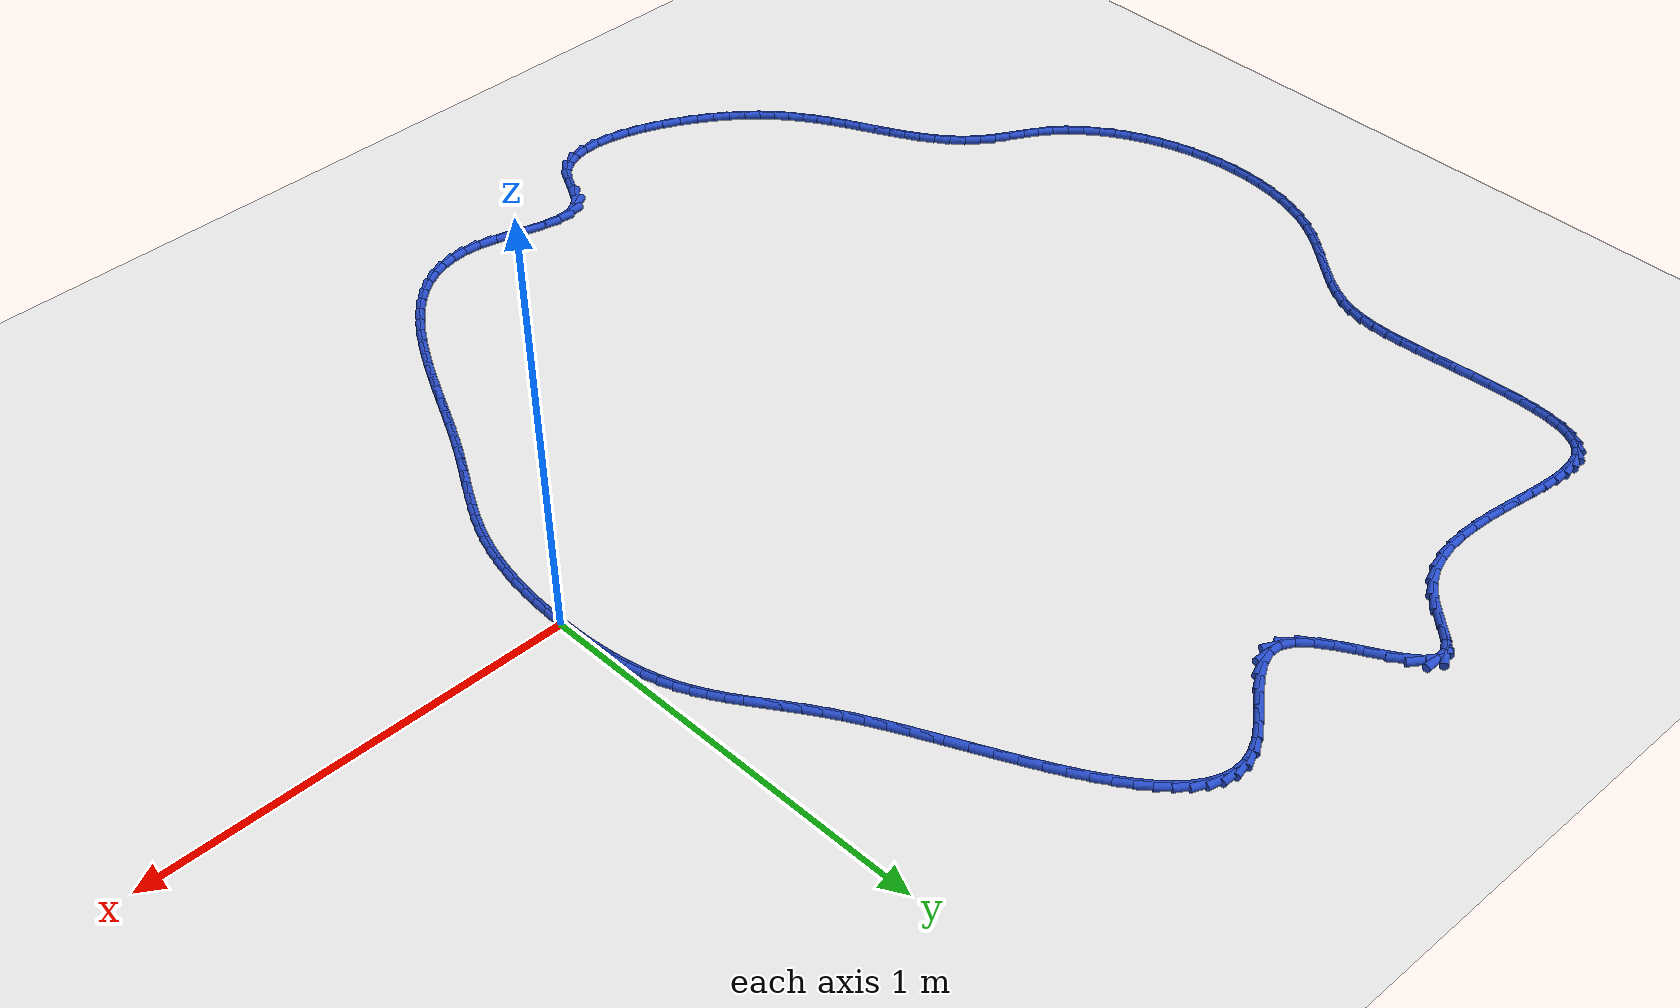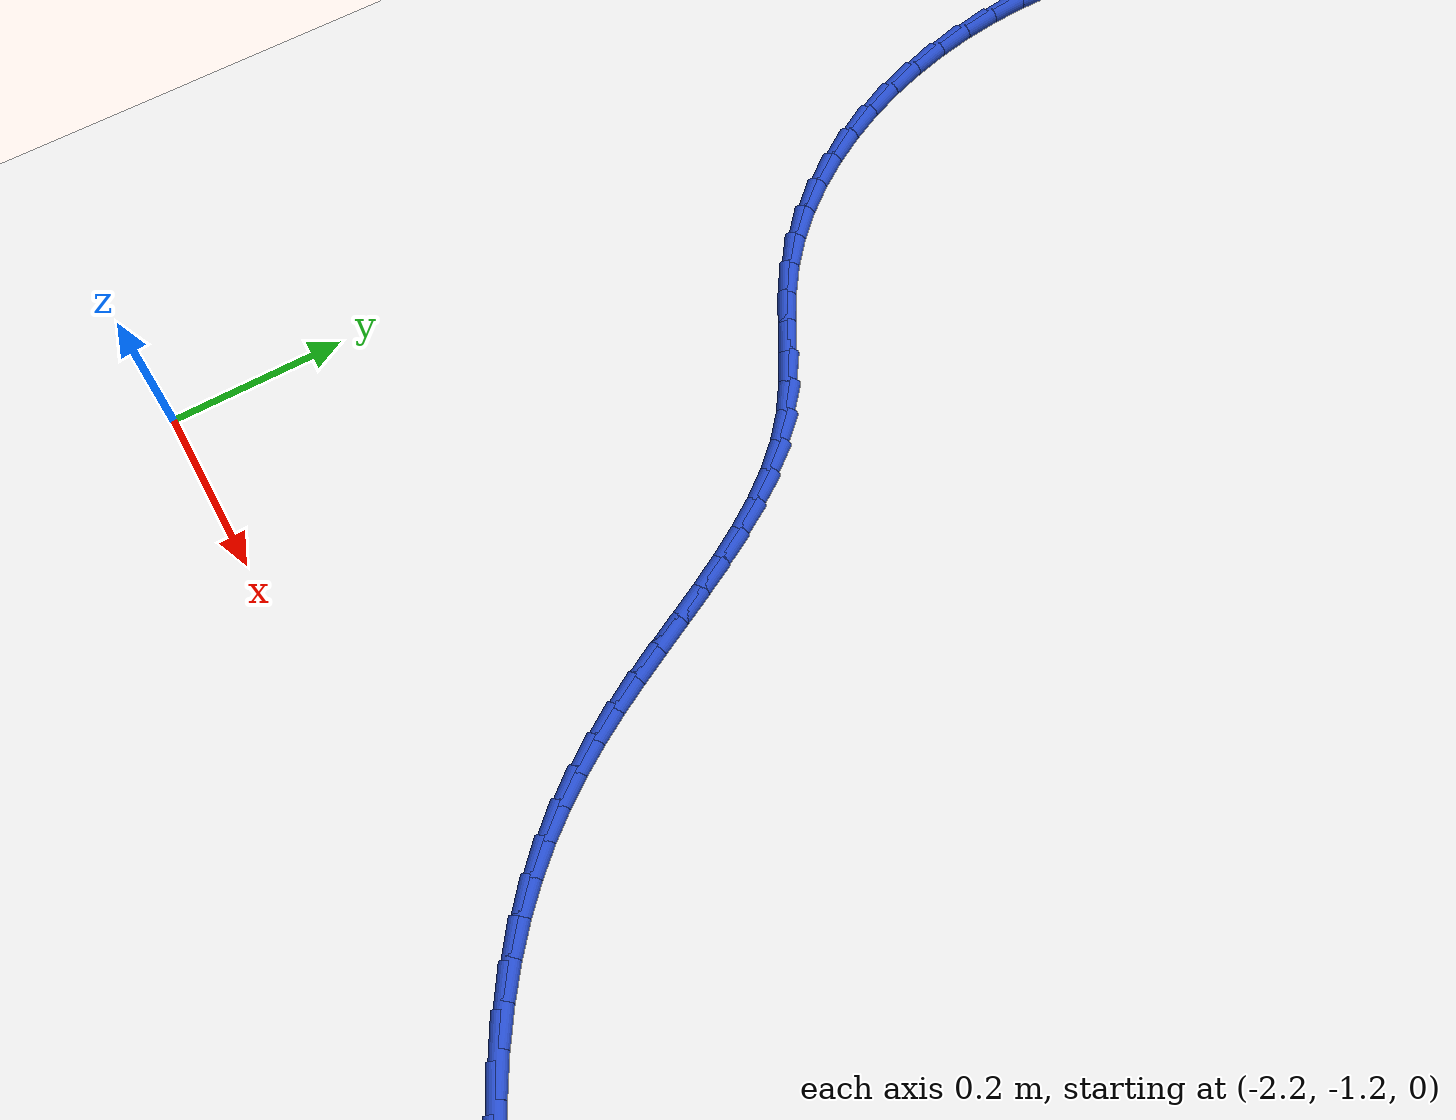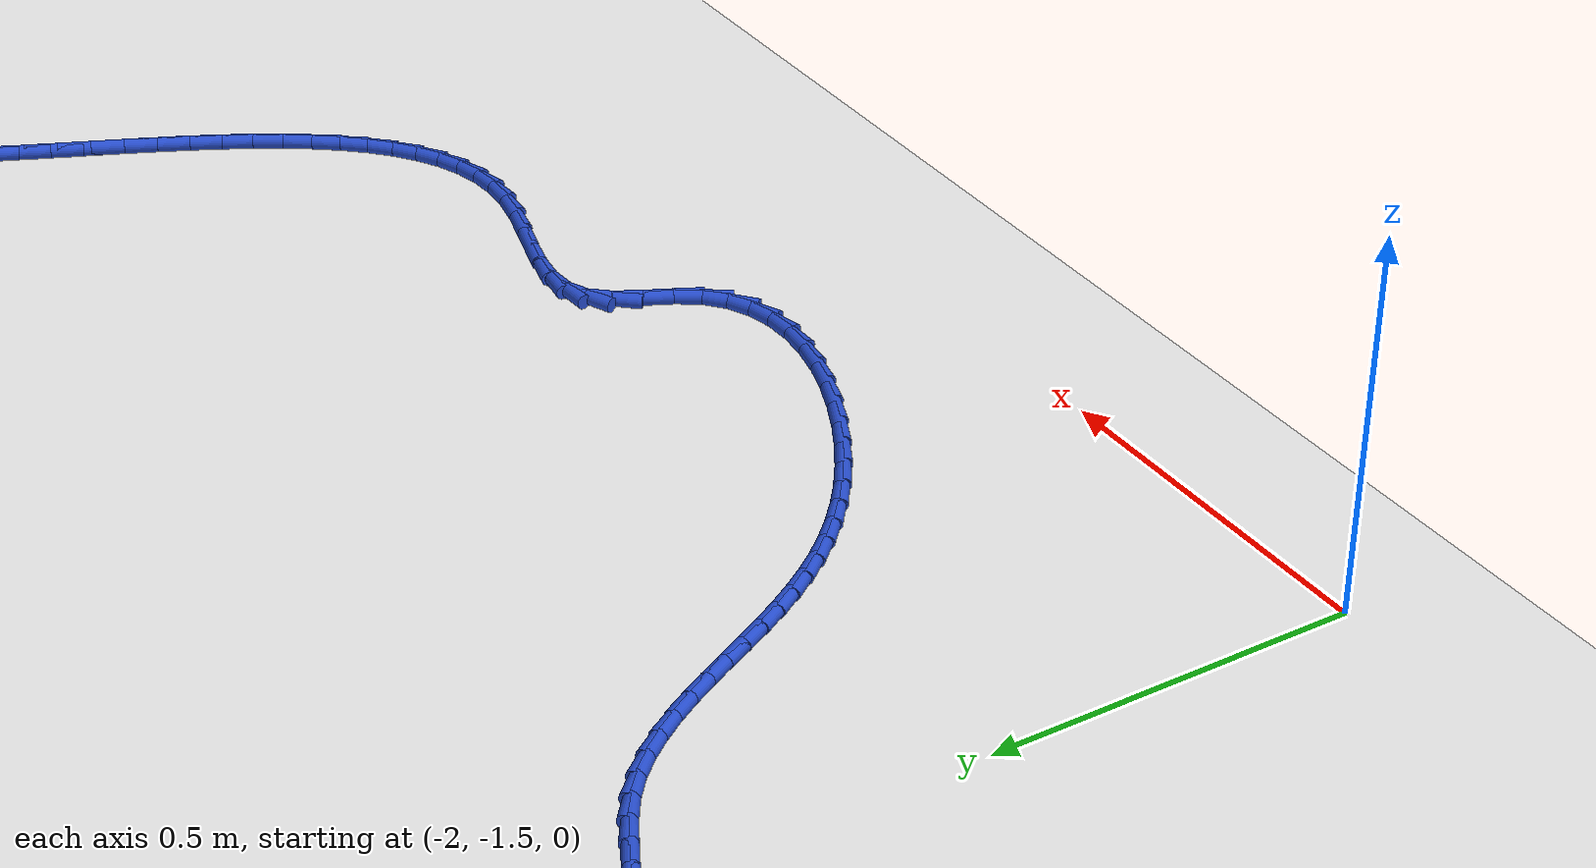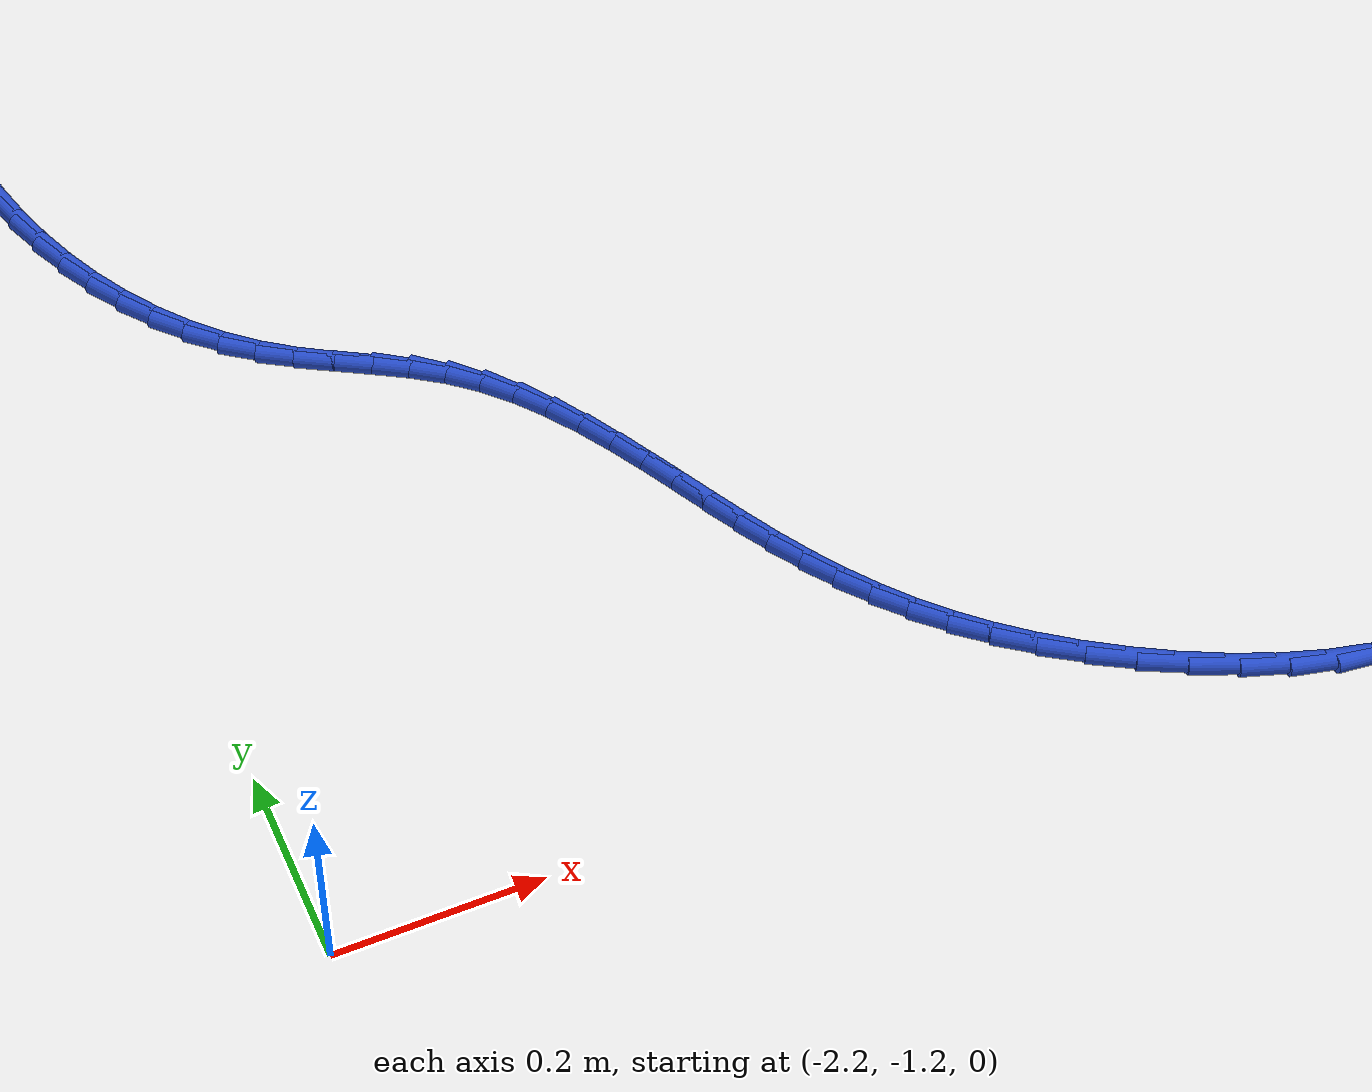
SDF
<sdf version="1.6">
 <world name="default">
  <light name="sun" type="directional">
   <pose>0 0 10 0 -0 0</pose>
   <diffuse>0.8 0.8 0.8 1</diffuse>
   <specular>0.2 0.2 0.2 1</specular>
   <attenuation>
    <range>1000</range>
    <constant>0.9</constant>
    <linear>0.01</linear>
    <quadratic>0.001</quadratic>
   </attenuation>
   <direction>-0.5 0.1 -0.9</direction>
  </light>
  <model name="ground_plane">
   <static>1</static>
   <link name="link">
    <collision name="collision">
     <geometry><plane><normal>0 0 1</normal><size>100 100</size></plane></geometry>
     <surface><friction><ode><mu>100</mu><mu2>50</mu2></ode></friction></surface>
    </collision>
    <visual name="visual">
     <cast_shadows>0</cast_shadows>
     <geometry><plane><normal>0 0 1</normal><size>100 100</size></plane></geometry>
     <material>
      <script><uri>file://media/materials/scripts/gazebo.material</uri><name>Gazebo/WhiteGlow</name></script>
     </material>
    </visual>
   </link>
  </model>
  <gravity>0 0 -9.8</gravity>
  <magnetic_field>6e-06 2.3e-05 -4.2e-05</magnetic_field>
  <atmosphere type="adiabatic"/>
  <physics name="default_physics" default="0" type="ode">
   <max_step_size>0.001</max_step_size>
   <real_time_factor>1</real_time_factor>
   <real_time_update_rate>1000</real_time_update_rate>
  </physics>
  <scene><ambient>0.4 0.4 0.4 1</ambient><background>0.7 0.7 0.7 1</background><shadows>1</shadows></scene>
  <spherical_coordinates>
   <surface_model>EARTH_WGS84</surface_model>
   <latitude_deg>0</latitude_deg>
   <longitude_deg>0</longitude_deg>
   <elevation>0</elevation>
   <heading_deg>0</heading_deg>
  </spherical_coordinates>
  <model name="line">
   <link name="link_0">
    <pose>-1.734723475976807e-18 -6.938893903907228e-17 0.01 0 1.57 -1.563096844219705</pose>
    <collision name="collision">
     <geometry><cylinder><radius>0.01</radius><length>0.08</length></cylinder></geometry>
    </collision>
    <visual name="visual">
     <material>
      <script><name>Gazebo/Blue</name><uri>file://media/materials/scripts/gazebo.material</uri></script>
     </material>
     <geometry><cylinder><radius>0.01</radius><length>0.08</length></cylinder></geometry>
    </visual>
   </link>
   <link name="link_1">
    <pose>-0.0003049578047452605 0.03960678858229409 0.01 0 1.57 -1.530554185920481</pose>
    <collision name="collision">
     <geometry><cylinder><radius>0.01</radius><length>0.08</length></cylinder></geometry>
    </collision>
    <visual name="visual">
     <material>
      <script><name>Gazebo/Blue</name><uri>file://media/materials/scripts/gazebo.material</uri></script>
     </material>
     <geometry><cylinder><radius>0.01</radius><length>0.08</length></cylinder></geometry>
    </visual>
   </link>
   <link name="link_2">
    <pose>-0.0018966604278241087 0.07913856494392668 0.01 0 1.57 -1.49403480154103</pose>
    <collision name="collision">
     <geometry><cylinder><radius>0.01</radius><length>0.08</length></cylinder></geometry>
    </collision>
    <visual name="visual">
     <material>
      <script><name>Gazebo/Blue</name><uri>file://media/materials/scripts/gazebo.material</uri></script>
     </material>
     <geometry><cylinder><radius>0.01</radius><length>0.08</length></cylinder></geometry>
    </visual>
   </link>
   <link name="link_3">
    <pose>-0.004914437785738147 0.11837498930932815 0.01 0 1.57 -1.452979437839179</pose>
    <collision name="collision">
     <geometry><cylinder><radius>0.01</radius><length>0.08</length></cylinder></geometry>
    </collision>
    <visual name="visual">
     <material>
      <script><name>Gazebo/Blue</name><uri>file://media/materials/scripts/gazebo.material</uri></script>
     </material>
     <geometry><cylinder><radius>0.01</radius><length>0.08</length></cylinder></geometry>
    </visual>
   </link>
   <link name="link_4">
    <pose>-0.009497619794988981 0.157095721902929 0.01 0 1.57 -1.40674588054292</pose>
    <collision name="collision">
     <geometry><cylinder><radius>0.01</radius><length>0.08</length></cylinder></geometry>
    </collision>
    <visual name="visual">
     <material>
      <script><name>Gazebo/Blue</name><uri>file://media/materials/scripts/gazebo.material</uri></script>
     </material>
     <geometry><cylinder><radius>0.01</radius><length>0.08</length></cylinder></geometry>
    </visual>
   </link>
   <link name="link_5">
    <pose>-0.0157855363720782 0.19508042294915962 0.01 0 1.57 -1.354613163608315</pose>
    <collision name="collision">
     <geometry><cylinder><radius>0.01</radius><length>0.08</length></cylinder></geometry>
    </collision>
    <visual name="visual">
     <material>
      <script><name>Gazebo/Blue</name><uri>file://media/materials/scripts/gazebo.material</uri></script>
     </material>
     <geometry><cylinder><radius>0.01</radius><length>0.08</length></cylinder></geometry>
    </visual>
   </link>
   <link name="link_6">
    <pose>-0.02391751743350742 0.23210875267245074 0.01 0 1.57 -1.2957991453305557</pose>
    <collision name="collision">
     <geometry><cylinder><radius>0.01</radius><length>0.08</length></cylinder></geometry>
    </collision>
    <visual name="visual">
     <material>
      <script><name>Gazebo/Blue</name><uri>file://media/materials/scripts/gazebo.material</uri></script>
     </material>
     <geometry><cylinder><radius>0.01</radius><length>0.08</length></cylinder></geometry>
    </visual>
   </link>
   <link name="link_7">
    <pose>-0.03403289289577824 0.2679603712972326 0.01 0 1.57 -1.229500715353914</pose>
    <collision name="collision">
     <geometry><cylinder><radius>0.01</radius><length>0.08</length></cylinder></geometry>
    </collision>
    <visual name="visual">
     <material>
      <script><name>Gazebo/Blue</name><uri>file://media/materials/scripts/gazebo.material</uri></script>
     </material>
     <geometry><cylinder><radius>0.01</radius><length>0.08</length></cylinder></geometry>
    </visual>
   </link>
   <link name="link_8">
    <pose>-0.04627099267539225 0.30241493904793587 0.01 0 1.57 -1.15666936004901</pose>
    <collision name="collision">
     <geometry><cylinder><radius>0.01</radius><length>0.08</length></cylinder></geometry>
    </collision>
    <visual name="visual">
     <material>
      <script><name>Gazebo/Blue</name><uri>file://media/materials/scripts/gazebo.material</uri></script>
     </material>
     <geometry><cylinder><radius>0.01</radius><length>0.08</length></cylinder></geometry>
    </visual>
   </link>
   <link name="link_9">
    <pose>-0.06073254444390269 0.33531600388133 0.01 0 1.57 -1.0902655378315615</pose>
    <collision name="collision">
     <geometry><cylinder><radius>0.01</radius><length>0.08</length></cylinder></geometry>
    </collision>
    <visual name="visual">
     <material>
      <script><name>Gazebo/Blue</name><uri>file://media/materials/scripts/gazebo.material</uri></script>
     </material>
     <geometry><cylinder><radius>0.01</radius><length>0.08</length></cylinder></geometry>
    </visual>
   </link>
   <link name="link_10">
    <pose>-0.07723576086874107 0.36697468352867046 0.01 0 1.57 -1.0381031123624456</pose>
    <collision name="collision">
     <geometry><cylinder><radius>0.01</radius><length>0.08</length></cylinder></geometry>
    </collision>
    <visual name="visual">
     <material>
      <script><name>Gazebo/Blue</name><uri>file://media/materials/scripts/gazebo.material</uri></script>
     </material>
     <geometry><cylinder><radius>0.01</radius><length>0.08</length></cylinder></geometry>
    </visual>
   </link>
   <link name="link_11">
    <pose>-0.0954733101461299 0.3979098751284458 0.01 0 1.57 -1.0015802505360922</pose>
    <collision name="collision">
     <geometry><cylinder><radius>0.01</radius><length>0.08</length></cylinder></geometry>
    </collision>
    <visual name="visual">
     <material>
      <script><name>Gazebo/Blue</name><uri>file://media/materials/scripts/gazebo.material</uri></script>
     </material>
     <geometry><cylinder><radius>0.01</radius><length>0.08</length></cylinder></geometry>
    </visual>
   </link>
   <link name="link_12">
    <pose>-0.11513729105276577 0.4286414182234618 0.01 0 1.57 -0.9809225280966541</pose>
    <collision name="collision">
     <geometry><cylinder><radius>0.01</radius><length>0.08</length></cylinder></geometry>
    </collision>
    <visual name="visual">
     <material>
      <script><name>Gazebo/Blue</name><uri>file://media/materials/scripts/gazebo.material</uri></script>
     </material>
     <geometry><cylinder><radius>0.01</radius><length>0.08</length></cylinder></geometry>
    </visual>
   </link>
   <link name="link_13">
    <pose>-0.13591980236534504 0.45968915235652397 0.01 0 1.57 -0.9755055367433808</pose>
    <collision name="collision">
     <geometry><cylinder><radius>0.01</radius><length>0.08</length></cylinder></geometry>
    </collision>
    <visual name="visual">
     <material>
      <script><name>Gazebo/Blue</name><uri>file://media/materials/scripts/gazebo.material</uri></script>
     </material>
     <geometry><cylinder><radius>0.01</radius><length>0.08</length></cylinder></geometry>
    </visual>
   </link>
   <link name="link_14">
    <pose>-0.1575129428605643 0.49157291707043804 0.01 0 1.57 -0.9841255510834079</pose>
    <collision name="collision">
     <geometry><cylinder><radius>0.01</radius><length>0.08</length></cylinder></geometry>
    </collision>
    <visual name="visual">
     <material>
      <script><name>Gazebo/Blue</name><uri>file://media/materials/scripts/gazebo.material</uri></script>
     </material>
     <geometry><cylinder><radius>0.01</radius><length>0.08</length></cylinder></geometry>
    </visual>
   </link>
   <link name="link_15">
    <pose>-0.17960881131511974 0.5248125519080092 0.01 0 1.57 -1.005191505480395</pose>
    <collision name="collision">
     <geometry><cylinder><radius>0.01</radius><length>0.08</length></cylinder></geometry>
    </collision>
    <visual name="visual">
     <material>
      <script><name>Gazebo/Blue</name><uri>file://media/materials/scripts/gazebo.material</uri></script>
     </material>
     <geometry><cylinder><radius>0.01</radius><length>0.08</length></cylinder></geometry>
    </visual>
   </link>
   <link name="link_16">
    <pose>-0.2018995065057081 0.5599278964120434 0.01 0 1.57 -1.0368095923707983</pose>
    <collision name="collision">
     <geometry><cylinder><radius>0.01</radius><length>0.08</length></cylinder></geometry>
    </collision>
    <visual name="visual">
     <material>
      <script><name>Gazebo/Blue</name><uri>file://media/materials/scripts/gazebo.material</uri></script>
     </material>
     <geometry><cylinder><radius>0.01</radius><length>0.08</length></cylinder></geometry>
    </visual>
   </link>
   <link name="link_17">
    <pose>-0.22407790621806453 0.5974367143042708 0.01 0 1.57 -1.0714455766708502</pose>
    <collision name="collision">
     <geometry><cylinder><radius>0.01</radius><length>0.08</length></cylinder></geometry>
    </collision>
    <visual name="visual">
     <material>
      <script><name>Gazebo/Blue</name><uri>file://media/materials/scripts/gazebo.material</uri></script>
     </material>
     <geometry><cylinder><radius>0.01</radius><length>0.08</length></cylinder></geometry>
    </visual>
   </link>
   <link name="link_18">
    <pose>-0.24595448917882934 0.6375433987299491 0.01 0 1.57 -1.0978116059196539</pose>
    <collision name="collision">
     <geometry><cylinder><radius>0.01</radius><length>0.08</length></cylinder></geometry>
    </collision>
    <visual name="visual">
     <material>
      <script><name>Gazebo/Blue</name><uri>file://media/materials/scripts/gazebo.material</uri></script>
     </material>
     <geometry><cylinder><radius>0.01</radius><length>0.08</length></cylinder></geometry>
    </visual>
   </link>
   <link name="link_19">
    <pose>-0.26758190669674775 0.6798070268948878 0.01 0 1.57 -1.1161051125901118</pose>
    <collision name="collision">
     <geometry><cylinder><radius>0.01</radius><length>0.08</length></cylinder></geometry>
    </collision>
    <visual name="visual">
     <material>
      <script><name>Gazebo/Blue</name><uri>file://media/materials/scripts/gazebo.material</uri></script>
     </material>
     <geometry><cylinder><radius>0.01</radius><length>0.08</length></cylinder></geometry>
    </visual>
   </link>
   <link name="link_20">
    <pose>-0.28904265806325685 0.723707140250583 0.01 0 1.57 -1.1274582312763621</pose>
    <collision name="collision">
     <geometry><cylinder><radius>0.01</radius><length>0.08</length></cylinder></geometry>
    </collision>
    <visual name="visual">
     <material>
      <script><name>Gazebo/Blue</name><uri>file://media/materials/scripts/gazebo.material</uri></script>
     </material>
     <geometry><cylinder><radius>0.01</radius><length>0.08</length></cylinder></geometry>
    </visual>
   </link>
   <link name="link_21">
    <pose>-0.3104192425697938 0.7687232802485314 0.01 0 1.57 -1.1325599127170403</pose>
    <collision name="collision">
     <geometry><cylinder><radius>0.01</radius><length>0.08</length></cylinder></geometry>
    </collision>
    <visual name="visual">
     <material>
      <script><name>Gazebo/Blue</name><uri>file://media/materials/scripts/gazebo.material</uri></script>
     </material>
     <geometry><cylinder><radius>0.01</radius><length>0.08</length></cylinder></geometry>
    </visual>
   </link>
   <link name="link_22">
    <pose>-0.3317941595077959 0.8143349883402293 0.01 0 1.57 -1.131741254754109</pose>
    <collision name="collision">
     <geometry><cylinder><radius>0.01</radius><length>0.08</length></cylinder></geometry>
    </collision>
    <visual name="visual">
     <material>
      <script><name>Gazebo/Blue</name><uri>file://media/materials/scripts/gazebo.material</uri></script>
     </material>
     <geometry><cylinder><radius>0.01</radius><length>0.08</length></cylinder></geometry>
    </visual>
   </link>
   <link name="link_23">
    <pose>-0.35324990816870006 0.8600218059771735 0.01 0 1.57 -1.1250172283286257</pose>
    <collision name="collision">
     <geometry><cylinder><radius>0.01</radius><length>0.08</length></cylinder></geometry>
    </collision>
    <visual name="visual">
     <material>
      <script><name>Gazebo/Blue</name><uri>file://media/materials/scripts/gazebo.material</uri></script>
     </material>
     <geometry><cylinder><radius>0.01</radius><length>0.08</length></cylinder></geometry>
    </visual>
   </link>
   <link name="link_24">
    <pose>-0.37486898784394357 0.9052632746108599 0.01 0 1.57 -1.1120921637251449</pose>
    <collision name="collision">
     <geometry><cylinder><radius>0.01</radius><length>0.08</length></cylinder></geometry>
    </collision>
    <visual name="visual">
     <material>
      <script><name>Gazebo/Blue</name><uri>file://media/materials/scripts/gazebo.material</uri></script>
     </material>
     <geometry><cylinder><radius>0.01</radius><length>0.08</length></cylinder></geometry>
    </visual>
   </link>
   <link name="link_25">
    <pose>-0.3967338978249636 0.9495389356927856 0.01 0 1.57 -1.0923307052964393</pose>
    <collision name="collision">
     <geometry><cylinder><radius>0.01</radius><length>0.08</length></cylinder></geometry>
    </collision>
    <visual name="visual">
     <material>
      <script><name>Gazebo/Blue</name><uri>file://media/materials/scripts/gazebo.material</uri></script>
     </material>
     <geometry><cylinder><radius>0.01</radius><length>0.08</length></cylinder></geometry>
    </visual>
   </link>
   <link name="link_26">
    <pose>-0.41892713740319754 0.9923283306744473 0.01 0 1.57 -1.0646908877710606</pose>
    <collision name="collision">
     <geometry><cylinder><radius>0.01</radius><length>0.08</length></cylinder></geometry>
    </collision>
    <visual name="visual">
     <material>
      <script><name>Gazebo/Blue</name><uri>file://media/materials/scripts/gazebo.material</uri></script>
     </material>
     <geometry><cylinder><radius>0.01</radius><length>0.08</length></cylinder></geometry>
    </visual>
   </link>
   <link name="link_27">
    <pose>-0.44153120587008227 1.0331110010073412 0.01 0 1.57 -1.0276116539149918</pose>
    <collision name="collision">
     <geometry><cylinder><radius>0.01</radius><length>0.08</length></cylinder></geometry>
    </collision>
    <visual name="visual">
     <material>
      <script><name>Gazebo/Blue</name><uri>file://media/materials/scripts/gazebo.material</uri></script>
     </material>
     <geometry><cylinder><radius>0.01</radius><length>0.08</length></cylinder></geometry>
    </visual>
   </link>
   <link name="link_28">
    <pose>-0.46462860251705507 1.0713664881429636 0.01 0 1.57 -0.9788453771743366</pose>
    <collision name="collision">
     <geometry><cylinder><radius>0.01</radius><length>0.08</length></cylinder></geometry>
    </collision>
    <visual name="visual">
     <material>
      <script><name>Gazebo/Blue</name><uri>file://media/materials/scripts/gazebo.material</uri></script>
     </material>
     <geometry><cylinder><radius>0.01</radius><length>0.08</length></cylinder></geometry>
    </visual>
   </link>
   <link name="link_29">
    <pose>-0.4883018266355527 1.106574333532811 0.01 0 1.57 -0.9152340418354592</pose>
    <collision name="collision">
     <geometry><cylinder><radius>0.01</radius><length>0.08</length></cylinder></geometry>
    </collision>
    <visual name="visual">
     <material>
      <script><name>Gazebo/Blue</name><uri>file://media/materials/scripts/gazebo.material</uri></script>
     </material>
     <geometry><cylinder><radius>0.01</radius><length>0.08</length></cylinder></geometry>
    </visual>
   </link>
   <link name="link_30">
    <pose>-0.5126333775170131 1.1382140786283805 0.01 0 1.57 -0.8324679215887505</pose>
    <collision name="collision">
     <geometry><cylinder><radius>0.01</radius><length>0.08</length></cylinder></geometry>
    </collision>
    <visual name="visual">
     <material>
      <script><name>Gazebo/Blue</name><uri>file://media/materials/scripts/gazebo.material</uri></script>
     </material>
     <geometry><cylinder><radius>0.01</radius><length>0.08</length></cylinder></geometry>
    </visual>
   </link>
   <link name="link_31">
    <pose>-0.5377057544528729 1.1657652648811685 0.01 0 1.57 -0.7249954370144526</pose>
    <collision name="collision">
     <geometry><cylinder><radius>0.01</radius><length>0.08</length></cylinder></geometry>
    </collision>
    <visual name="visual">
     <material>
      <script><name>Gazebo/Blue</name><uri>file://media/materials/scripts/gazebo.material</uri></script>
     </material>
     <geometry><cylinder><radius>0.01</radius><length>0.08</length></cylinder></geometry>
    </visual>
   </link>
   <link name="link_32">
    <pose>-0.5636014567345694 1.1887074337426704 0.01 0 1.57 -0.5865807729079314</pose>
    <collision name="collision">
     <geometry><cylinder><radius>0.01</radius><length>0.08</length></cylinder></geometry>
    </collision>
    <visual name="visual">
     <material>
      <script><name>Gazebo/Blue</name><uri>file://media/materials/scripts/gazebo.material</uri></script>
     </material>
     <geometry><cylinder><radius>0.01</radius><length>0.08</length></cylinder></geometry>
    </visual>
   </link>
   <link name="link_33">
    <pose>-0.5904029836535398 1.2065201266643841 0.01 0 1.57 -0.4125523484968078</pose>
    <collision name="collision">
     <geometry><cylinder><radius>0.01</radius><length>0.08</length></cylinder></geometry>
    </collision>
    <visual name="visual">
     <material>
      <script><name>Gazebo/Blue</name><uri>file://media/materials/scripts/gazebo.material</uri></script>
     </material>
     <geometry><cylinder><radius>0.01</radius><length>0.08</length></cylinder></geometry>
    </visual>
   </link>
   <link name="link_34">
    <pose>-0.6181928345012214 1.2186828850978058 0.01 0 1.57 -0.2047220033296333</pose>
    <collision name="collision">
     <geometry><cylinder><radius>0.01</radius><length>0.08</length></cylinder></geometry>
    </collision>
    <visual name="visual">
     <material>
      <script><name>Gazebo/Blue</name><uri>file://media/materials/scripts/gazebo.material</uri></script>
     </material>
     <geometry><cylinder><radius>0.01</radius><length>0.08</length></cylinder></geometry>
    </visual>
   </link>
   <link name="link_35">
    <pose>-0.647053508569051 1.2246752504944314 0.01 0 1.57 0.023267815428800014</pose>
    <collision name="collision">
     <geometry><cylinder><radius>0.01</radius><length>0.08</length></cylinder></geometry>
    </collision>
    <visual name="visual">
     <material>
      <script><name>Gazebo/Blue</name><uri>file://media/materials/scripts/gazebo.material</uri></script>
     </material>
     <geometry><cylinder><radius>0.01</radius><length>0.08</length></cylinder></geometry>
    </visual>
   </link>
   <link name="link_36">
    <pose>-0.6770675051484656 1.2239767643057577 0.01 0 1.57 0.24790822838531043</pose>
    <collision name="collision">
     <geometry><cylinder><radius>0.01</radius><length>0.08</length></cylinder></geometry>
    </collision>
    <visual name="visual">
     <material>
      <script><name>Gazebo/Blue</name><uri>file://media/materials/scripts/gazebo.material</uri></script>
     </material>
     <geometry><cylinder><radius>0.01</radius><length>0.08</length></cylinder></geometry>
    </visual>
   </link>
   <link name="link_37">
    <pose>-0.7083173235309033 1.2160669679832816 0.01 0 1.57 0.4476300454967805</pose>
    <collision name="collision">
     <geometry><cylinder><radius>0.01</radius><length>0.08</length></cylinder></geometry>
    </collision>
    <visual name="visual">
     <material>
      <script><name>Gazebo/Blue</name><uri>file://media/materials/scripts/gazebo.material</uri></script>
     </material>
     <geometry><cylinder><radius>0.01</radius><length>0.08</length></cylinder></geometry>
    </visual>
   </link>
   <link name="link_38">
    <pose>-0.7408847157441301 1.2004302088681684 0.01 0 1.57 0.5937727301959914</pose>
    <collision name="collision">
     <geometry><cylinder><radius>0.01</radius><length>0.08</length></cylinder></geometry>
    </collision>
    <visual name="visual">
     <material>
      <script><name>Gazebo/Blue</name><uri>file://media/materials/scripts/gazebo.material</uri></script>
     </material>
     <geometry><cylinder><radius>0.01</radius><length>0.08</length></cylinder></geometry>
    </visual>
   </link>
   <link name="link_39">
    <pose>-0.7746862752528323 1.1776130214034166 0.01 0 1.57 0.6639849081857786</pose>
    <collision name="collision">
     <geometry><cylinder><radius>0.01</radius><length>0.08</length></cylinder></geometry>
    </collision>
    <visual name="visual">
     <material>
      <script><name>Gazebo/Blue</name><uri>file://media/materials/scripts/gazebo.material</uri></script>
     </material>
     <geometry><cylinder><radius>0.01</radius><length>0.08</length></cylinder></geometry>
    </visual>
   </link>
   <link name="link_40">
    <pose>-0.8092667393685598 1.1505534648929159 0.01 0 1.57 0.6774342985067893</pose>
    <collision name="collision">
     <geometry><cylinder><radius>0.01</radius><length>0.08</length></cylinder></geometry>
    </collision>
    <visual name="visual">
     <material>
      <script><name>Gazebo/Blue</name><uri>file://media/materials/scripts/gazebo.material</uri></script>
     </material>
     <geometry><cylinder><radius>0.01</radius><length>0.08</length></cylinder></geometry>
    </visual>
   </link>
   <link name="link_41">
    <pose>-0.8441200050574201 1.1225165690269128 0.01 0 1.57 0.6395003853780693</pose>
    <collision name="collision">
     <geometry><cylinder><radius>0.01</radius><length>0.08</length></cylinder></geometry>
    </collision>
    <visual name="visual">
     <material>
      <script><name>Gazebo/Blue</name><uri>file://media/materials/scripts/gazebo.material</uri></script>
     </material>
     <geometry><cylinder><radius>0.01</radius><length>0.08</length></cylinder></geometry>
    </visual>
   </link>
   <link name="link_42">
    <pose>-0.878739969285522 1.096767363495655 0.01 0 1.57 0.5375530999956624</pose>
    <collision name="collision">
     <geometry><cylinder><radius>0.01</radius><length>0.08</length></cylinder></geometry>
    </collision>
    <visual name="visual">
     <material>
      <script><name>Gazebo/Blue</name><uri>file://media/materials/scripts/gazebo.material</uri></script>
     </material>
     <geometry><cylinder><radius>0.01</radius><length>0.08</length></cylinder></geometry>
    </visual>
   </link>
   <link name="link_43">
    <pose>-0.9126205290189733 1.0765708779893886 0.01 0 1.57 0.3354859799048498</pose>
    <collision name="collision">
     <geometry><cylinder><radius>0.01</radius><length>0.08</length></cylinder></geometry>
    </collision>
    <visual name="visual">
     <material>
      <script><name>Gazebo/Blue</name><uri>file://media/materials/scripts/gazebo.material</uri></script>
     </material>
     <geometry><cylinder><radius>0.01</radius><length>0.08</length></cylinder></geometry>
    </visual>
   </link>
   <link name="link_44">
    <pose>-0.945255581223882 1.0651921421983603 0.01 0 1.57 -0.0227928512047549</pose>
    <collision name="collision">
     <geometry><cylinder><radius>0.01</radius><length>0.08</length></cylinder></geometry>
    </collision>
    <visual name="visual">
     <material>
      <script><name>Gazebo/Blue</name><uri>file://media/materials/scripts/gazebo.material</uri></script>
     </material>
     <geometry><cylinder><radius>0.01</radius><length>0.08</length></cylinder></geometry>
    </visual>
   </link>
   <link name="link_45">
    <pose>-0.9761390228663565 1.0658961858128178 0.01 0 1.57 -0.49437761989659157</pose>
    <collision name="collision">
     <geometry><cylinder><radius>0.01</radius><length>0.08</length></cylinder></geometry>
    </collision>
    <visual name="visual">
     <material>
      <script><name>Gazebo/Blue</name><uri>file://media/materials/scripts/gazebo.material</uri></script>
     </material>
     <geometry><cylinder><radius>0.01</radius><length>0.08</length></cylinder></geometry>
    </visual>
   </link>
   <link name="link_46">
    <pose>-1.0048362805057915 1.0813647081422098 0.01 0 1.57 -0.8147684012159502</pose>
    <collision name="collision">
     <geometry><cylinder><radius>0.01</radius><length>0.08</length></cylinder></geometry>
    </collision>
    <visual name="visual">
     <material>
      <script><name>Gazebo/Blue</name><uri>file://media/materials/scripts/gazebo.material</uri></script>
     </material>
     <geometry><cylinder><radius>0.01</radius><length>0.08</length></cylinder></geometry>
    </visual>
   </link>
   <link name="link_47">
    <pose>-1.0314835109664342 1.1096250509436865 0.01 0 1.57 -0.974588011661386</pose>
    <collision name="collision">
     <geometry><cylinder><radius>0.01</radius><length>0.08</length></cylinder></geometry>
    </collision>
    <visual name="visual">
     <material>
      <script><name>Gazebo/Blue</name><uri>file://media/materials/scripts/gazebo.material</uri></script>
     </material>
     <geometry><cylinder><radius>0.01</radius><length>0.08</length></cylinder></geometry>
    </visual>
   </link>
   <link name="link_48">
    <pose>-1.0564901218416407 1.1464761709399847 0.01 0 1.57 -1.047657138661661</pose>
    <collision name="collision">
     <geometry><cylinder><radius>0.01</radius><length>0.08</length></cylinder></geometry>
    </collision>
    <visual name="visual">
     <material>
      <script><name>Gazebo/Blue</name><uri>file://media/materials/scripts/gazebo.material</uri></script>
     </material>
     <geometry><cylinder><radius>0.01</radius><length>0.08</length></cylinder></geometry>
    </visual>
   </link>
   <link name="link_49">
    <pose>-1.0802672309870938 1.1877030775080313 0.01 0 1.57 -1.0643339725079486</pose>
    <collision name="collision">
     <geometry><cylinder><radius>0.01</radius><length>0.08</length></cylinder></geometry>
    </collision>
    <visual name="visual">
     <material>
      <script><name>Gazebo/Blue</name><uri>file://media/materials/scripts/gazebo.material</uri></script>
     </material>
     <geometry><cylinder><radius>0.01</radius><length>0.08</length></cylinder></geometry>
    </visual>
   </link>
   <link name="link_50">
    <pose>-1.1032259562584747 1.2290907800247532 0.01 0 1.57 -1.027401186385243</pose>
    <collision name="collision">
     <geometry><cylinder><radius>0.01</radius><length>0.08</length></cylinder></geometry>
    </collision>
    <visual name="visual">
     <material>
      <script><name>Gazebo/Blue</name><uri>file://media/materials/scripts/gazebo.material</uri></script>
     </material>
     <geometry><cylinder><radius>0.01</radius><length>0.08</length></cylinder></geometry>
    </visual>
   </link>
   <link name="link_51">
    <pose>-1.1257774155114655 1.266424287867077 0.01 0 1.57 -0.9108318097040208</pose>
    <collision name="collision">
     <geometry><cylinder><radius>0.01</radius><length>0.08</length></cylinder></geometry>
    </collision>
    <visual name="visual">
     <material>
      <script><name>Gazebo/Blue</name><uri>file://media/materials/scripts/gazebo.material</uri></script>
     </material>
     <geometry><cylinder><radius>0.01</radius><length>0.08</length></cylinder></geometry>
    </visual>
   </link>
   <link name="link_52">
    <pose>-1.1483327266017485 1.2954886104119305 0.01 0 1.57 -0.625213165758701</pose>
    <collision name="collision">
     <geometry><cylinder><radius>0.01</radius><length>0.08</length></cylinder></geometry>
    </collision>
    <visual name="visual">
     <material>
      <script><name>Gazebo/Blue</name><uri>file://media/materials/scripts/gazebo.material</uri></script>
     </material>
     <geometry><cylinder><radius>0.01</radius><length>0.08</length></cylinder></geometry>
    </visual>
   </link>
   <link name="link_53">
    <pose>-1.171303007385005 1.3120687570362397 0.01 0 1.57 -0.0005271589317777145</pose>
    <collision name="collision">
     <geometry><cylinder><radius>0.01</radius><length>0.08</length></cylinder></geometry>
    </collision>
    <visual name="visual">
     <material>
      <script><name>Gazebo/Blue</name><uri>file://media/materials/scripts/gazebo.material</uri></script>
     </material>
     <geometry><cylinder><radius>0.01</radius><length>0.08</length></cylinder></geometry>
    </visual>
   </link>
   <link name="link_54">
    <pose>-1.1950995946444856 1.3120813016209214 0.01 0 1.57 0.5793119580593432</pose>
    <collision name="collision">
     <geometry><cylinder><radius>0.01</radius><length>0.08</length></cylinder></geometry>
    </collision>
    <visual name="visual">
     <material>
      <script><name>Gazebo/Blue</name><uri>file://media/materials/scripts/gazebo.material</uri></script>
     </material>
     <geometry><cylinder><radius>0.01</radius><length>0.08</length></cylinder></geometry>
    </visual>
   </link>
   <link name="link_55">
    <pose>-1.2201409086468977 1.2956996368312537 0.01 0 1.57 0.8003394875678993</pose>
    <collision name="collision">
     <geometry><cylinder><radius>0.01</radius><length>0.08</length></cylinder></geometry>
    </collision>
    <visual name="visual">
     <material>
      <script><name>Gazebo/Blue</name><uri>file://media/materials/scripts/gazebo.material</uri></script>
     </material>
     <geometry><cylinder><radius>0.01</radius><length>0.08</length></cylinder></geometry>
    </visual>
   </link>
   <link name="link_56">
    <pose>-1.2468538215229554 1.2681763022928572 0.01 0 1.57 0.8547711497164949</pose>
    <collision name="collision">
     <geometry><cylinder><radius>0.01</radius><length>0.08</length></cylinder></geometry>
    </collision>
    <visual name="visual">
     <material>
      <script><name>Gazebo/Blue</name><uri>file://media/materials/scripts/gazebo.material</uri></script>
     </material>
     <geometry><cylinder><radius>0.01</radius><length>0.08</length></cylinder></geometry>
    </visual>
   </link>
   <link name="link_57">
    <pose>-1.2756657006860972 1.2350614777434699 0.01 0 1.57 0.8135780084928548</pose>
    <collision name="collision">
     <geometry><cylinder><radius>0.01</radius><length>0.08</length></cylinder></geometry>
    </collision>
    <visual name="visual">
     <material>
      <script><name>Gazebo/Blue</name><uri>file://media/materials/scripts/gazebo.material</uri></script>
     </material>
     <geometry><cylinder><radius>0.01</radius><length>0.08</length></cylinder></geometry>
    </visual>
   </link>
   <link name="link_58">
    <pose>-1.3070039135497633 1.201905342920831 0.01 0 1.57 0.6819323054271791</pose>
    <collision name="collision">
     <geometry><cylinder><radius>0.01</radius><length>0.08</length></cylinder></geometry>
    </collision>
    <visual name="visual">
     <material>
      <script><name>Gazebo/Blue</name><uri>file://media/materials/scripts/gazebo.material</uri></script>
     </material>
     <geometry><cylinder><radius>0.01</radius><length>0.08</length></cylinder></geometry>
    </visual>
   </link>
   <link name="link_59">
    <pose>-1.3412706739320068 1.1740854525393079 0.01 0 1.57 0.502146375810371</pose>
    <collision name="collision">
     <geometry><cylinder><radius>0.01</radius><length>0.08</length></cylinder></geometry>
    </collision>
    <visual name="visual">
     <material>
      <script><name>Gazebo/Blue</name><uri>file://media/materials/scripts/gazebo.material</uri></script>
     </material>
     <geometry><cylinder><radius>0.01</radius><length>0.08</length></cylinder></geometry>
    </visual>
   </link>
   <link name="link_60">
    <pose>-1.3783907984816914 1.1537030623896634 0.01 0 1.57 0.3357796123650263</pose>
    <collision name="collision">
     <geometry><cylinder><radius>0.01</radius><length>0.08</length></cylinder></geometry>
    </collision>
    <visual name="visual">
     <material>
      <script><name>Gazebo/Blue</name><uri>file://media/materials/scripts/gazebo.material</uri></script>
     </material>
     <geometry><cylinder><radius>0.01</radius><length>0.08</length></cylinder></geometry>
    </visual>
   </link>
   <link name="link_61">
    <pose>-1.4178619318707952 1.1399278166436846 0.01 0 1.57 0.1936899151199877</pose>
    <collision name="collision">
     <geometry><cylinder><radius>0.01</radius><length>0.08</length></cylinder></geometry>
    </collision>
    <visual name="visual">
     <material>
      <script><name>Gazebo/Blue</name><uri>file://media/materials/scripts/gazebo.material</uri></script>
     </material>
     <geometry><cylinder><radius>0.01</radius><length>0.08</length></cylinder></geometry>
    </visual>
   </link>
   <link name="link_62">
    <pose>-1.4591666491415352 1.1318259390614913 0.01 0 1.57 0.07872519266667492</pose>
    <collision name="collision">
     <geometry><cylinder><radius>0.01</radius><length>0.08</length></cylinder></geometry>
    </collision>
    <visual name="visual">
     <material>
      <script><name>Gazebo/Blue</name><uri>file://media/materials/scripts/gazebo.material</uri></script>
     </material>
     <geometry><cylinder><radius>0.01</radius><length>0.08</length></cylinder></geometry>
    </visual>
   </link>
   <link name="link_63">
    <pose>-1.501787525336128 1.128463653403203 0.01 0 1.57 -0.010214614969075142</pose>
    <collision name="collision">
     <geometry><cylinder><radius>0.01</radius><length>0.08</length></cylinder></geometry>
    </collision>
    <visual name="visual">
     <material>
      <script><name>Gazebo/Blue</name><uri>file://media/materials/scripts/gazebo.material</uri></script>
     </material>
     <geometry><cylinder><radius>0.01</radius><length>0.08</length></cylinder></geometry>
    </visual>
   </link>
   <link name="link_64">
    <pose>-1.5452071354967907 1.1289071834289406 0.01 0 1.57 -0.07572448661729395</pose>
    <collision name="collision">
     <geometry><cylinder><radius>0.01</radius><length>0.08</length></cylinder></geometry>
    </collision>
    <visual name="visual">
     <material>
      <script><name>Gazebo/Blue</name><uri>file://media/materials/scripts/gazebo.material</uri></script>
     </material>
     <geometry><cylinder><radius>0.01</radius><length>0.08</length></cylinder></geometry>
    </visual>
   </link>
   <link name="link_65">
    <pose>-1.5889080546657408 1.1322227528988231 0.01 0 1.57 -0.12029197287766909</pose>
    <collision name="collision">
     <geometry><cylinder><radius>0.01</radius><length>0.08</length></cylinder></geometry>
    </collision>
    <visual name="visual">
     <material>
      <script><name>Gazebo/Blue</name><uri>file://media/materials/scripts/gazebo.material</uri></script>
     </material>
     <geometry><cylinder><radius>0.01</radius><length>0.08</length></cylinder></geometry>
    </visual>
   </link>
   <link name="link_66">
    <pose>-1.6323728578851944 1.137476585572971 0.01 0 1.57 -0.14549088456201398</pose>
    <collision name="collision">
     <geometry><cylinder><radius>0.01</radius><length>0.08</length></cylinder></geometry>
    </collision>
    <visual name="visual">
     <material>
      <script><name>Gazebo/Blue</name><uri>file://media/materials/scripts/gazebo.material</uri></script>
     </material>
     <geometry><cylinder><radius>0.01</radius><length>0.08</length></cylinder></geometry>
    </visual>
   </link>
   <link name="link_67">
    <pose>-1.6750841201973694 1.1437349052115038 0.01 0 1.57 -0.1515553535691179</pose>
    <collision name="collision">
     <geometry><cylinder><radius>0.01</radius><length>0.08</length></cylinder></geometry>
    </collision>
    <visual name="visual">
     <material>
      <script><name>Gazebo/Blue</name><uri>file://media/materials/scripts/gazebo.material</uri></script>
     </material>
     <geometry><cylinder><radius>0.01</radius><length>0.08</length></cylinder></geometry>
    </visual>
   </link>
   <link name="link_68">
    <pose>-1.7165244166444822 1.150063935574542 0.01 0 1.57 -0.13698540591236893</pose>
    <collision name="collision">
     <geometry><cylinder><radius>0.01</radius><length>0.08</length></cylinder></geometry>
    </collision>
    <visual name="visual">
     <material>
      <script><name>Gazebo/Blue</name><uri>file://media/materials/scripts/gazebo.material</uri></script>
     </material>
     <geometry><cylinder><radius>0.01</radius><length>0.08</length></cylinder></geometry>
    </visual>
   </link>
   <link name="link_69">
    <pose>-1.7561763222687492 1.1555299004222048 0.01 0 1.57 -0.09793222679177693</pose>
    <collision name="collision">
     <geometry><cylinder><radius>0.01</radius><length>0.08</length></cylinder></geometry>
    </collision>
    <visual name="visual">
     <material>
      <script><name>Gazebo/Blue</name><uri>file://media/materials/scripts/gazebo.material</uri></script>
     </material>
     <geometry><cylinder><radius>0.01</radius><length>0.08</length></cylinder></geometry>
    </visual>
   </link>
   <link name="link_70">
    <pose>-1.793522412112388 1.1591990235146123 0.01 0 1.57 -0.027178347983233122</pose>
    <collision name="collision">
     <geometry><cylinder><radius>0.01</radius><length>0.08</length></cylinder></geometry>
    </collision>
    <visual name="visual">
     <material>
      <script><name>Gazebo/Blue</name><uri>file://media/materials/scripts/gazebo.material</uri></script>
     </material>
     <geometry><cylinder><radius>0.01</radius><length>0.08</length></cylinder></geometry>
    </visual>
   </link>
   <link name="link_71">
    <pose>-1.8280452612176155 1.1601375286118851 0.01 0 1.57 0.08719649545120903</pose>
    <collision name="collision">
     <geometry><cylinder><radius>0.01</radius><length>0.08</length></cylinder></geometry>
    </collision>
    <visual name="visual">
     <material>
      <script><name>Gazebo/Blue</name><uri>file://media/materials/scripts/gazebo.material</uri></script>
     </material>
     <geometry><cylinder><radius>0.01</radius><length>0.08</length></cylinder></geometry>
    </visual>
   </link>
   <link name="link_72">
    <pose>-1.8592274446266495 1.1574116394741427 0.01 0 1.57 0.2618878592426622</pose>
    <collision name="collision">
     <geometry><cylinder><radius>0.01</radius><length>0.08</length></cylinder></geometry>
    </collision>
    <visual name="visual">
     <material>
      <script><name>Gazebo/Blue</name><uri>file://media/materials/scripts/gazebo.material</uri></script>
     </material>
     <geometry><cylinder><radius>0.01</radius><length>0.08</length></cylinder></geometry>
    </visual>
   </link>
   <link name="link_73">
    <pose>-1.8865515373817052 1.150087579861505 0.01 0 1.57 0.510482784973028</pose>
    <collision name="collision">
     <geometry><cylinder><radius>0.01</radius><length>0.08</length></cylinder></geometry>
    </collision>
    <visual name="visual">
     <material>
      <script><name>Gazebo/Blue</name><uri>file://media/materials/scripts/gazebo.material</uri></script>
     </material>
     <geometry><cylinder><radius>0.01</radius><length>0.08</length></cylinder></geometry>
    </visual>
   </link>
   <link name="link_74">
    <pose>-1.909502429962027 1.1372352469454068 0.01 0 1.57 0.7979305055107412</pose>
    <collision name="collision">
     <geometry><cylinder><radius>0.01</radius><length>0.08</length></cylinder></geometry>
    </collision>
    <visual name="visual">
     <material>
      <script><name>Gazebo/Blue</name><uri>file://media/materials/scripts/gazebo.material</uri></script>
     </material>
     <geometry><cylinder><radius>0.01</radius><length>0.08</length></cylinder></geometry>
    </visual>
   </link>
   <link name="link_75">
    <pose>-1.9278673336695045 1.1184041660272357 0.01 0 1.57 1.0431768070291565</pose>
    <collision name="collision">
     <geometry><cylinder><radius>0.01</radius><length>0.08</length></cylinder></geometry>
    </collision>
    <visual name="visual">
     <material>
      <script><name>Gazebo/Blue</name><uri>file://media/materials/scripts/gazebo.material</uri></script>
     </material>
     <geometry><cylinder><radius>0.01</radius><length>0.08</length></cylinder></geometry>
    </visual>
   </link>
   <link name="link_76">
    <pose>-1.9420329208471954 1.0940948997058946 0.01 0 1.57 1.2276514301835388</pose>
    <collision name="collision">
     <geometry><cylinder><radius>0.01</radius><length>0.08</length></cylinder></geometry>
    </collision>
    <visual name="visual">
     <material>
      <script><name>Gazebo/Blue</name><uri>file://media/materials/scripts/gazebo.material</uri></script>
     </material>
     <geometry><cylinder><radius>0.01</radius><length>0.08</length></cylinder></geometry>
    </visual>
   </link>
   <link name="link_77">
    <pose>-1.9524564876396697 1.0649200543407962 0.01 0 1.57 1.3603970152675255</pose>
    <collision name="collision">
     <geometry><cylinder><radius>0.01</radius><length>0.08</length></cylinder></geometry>
    </collision>
    <visual name="visual">
     <material>
      <script><name>Gazebo/Blue</name><uri>file://media/materials/scripts/gazebo.material</uri></script>
     </material>
     <geometry><cylinder><radius>0.01</radius><length>0.08</length></cylinder></geometry>
    </visual>
   </link>
   <link name="link_78">
    <pose>-1.9595953301914972 1.031492236291354 0.01 0 1.57 1.4550062207638366</pose>
    <collision name="collision">
     <geometry><cylinder><radius>0.01</radius><length>0.08</length></cylinder></geometry>
    </collision>
    <visual name="visual">
     <material>
      <script><name>Gazebo/Blue</name><uri>file://media/materials/scripts/gazebo.material</uri></script>
     </material>
     <geometry><cylinder><radius>0.01</radius><length>0.08</length></cylinder></geometry>
    </visual>
   </link>
   <link name="link_79">
    <pose>-1.9639067446472491 0.9944240519169804 0.01 0 1.57 1.522418172570288</pose>
    <collision name="collision">
     <geometry><cylinder><radius>0.01</radius><length>0.08</length></cylinder></geometry>
    </collision>
    <visual name="visual">
     <material>
      <script><name>Gazebo/Blue</name><uri>file://media/materials/scripts/gazebo.material</uri></script>
     </material>
     <geometry><cylinder><radius>0.01</radius><length>0.08</length></cylinder></geometry>
    </visual>
   </link>
   <link name="link_80">
    <pose>-1.9658480271514955 0.9543281075770894 0.01 0 1.57 1.5701271675767041</pose>
    <collision name="collision">
     <geometry><cylinder><radius>0.01</radius><length>0.08</length></cylinder></geometry>
    </collision>
    <visual name="visual">
     <material>
      <script><name>Gazebo/Blue</name><uri>file://media/materials/scripts/gazebo.material</uri></script>
     </material>
     <geometry><cylinder><radius>0.01</radius><length>0.08</length></cylinder></geometry>
    </visual>
   </link>
   <link name="link_81">
    <pose>-1.9658764738488075 0.911817009631094 0.01 0 1.57 -1.538603084523212</pose>
    <collision name="collision">
     <geometry><cylinder><radius>0.01</radius><length>0.08</length></cylinder></geometry>
    </collision>
    <visual name="visual">
     <material>
      <script><name>Gazebo/Blue</name><uri>file://media/materials/scripts/gazebo.material</uri></script>
     </material>
     <geometry><cylinder><radius>0.01</radius><length>0.08</length></cylinder></geometry>
    </visual>
   </link>
   <link name="link_82">
    <pose>-1.9644493808837544 0.8675033644384074 0.01 0 1.57 -1.517546816096129</pose>
    <collision name="collision">
     <geometry><cylinder><radius>0.01</radius><length>0.08</length></cylinder></geometry>
    </collision>
    <visual name="visual">
     <material>
      <script><name>Gazebo/Blue</name><uri>file://media/materials/scripts/gazebo.material</uri></script>
     </material>
     <geometry><cylinder><radius>0.01</radius><length>0.08</length></cylinder></geometry>
    </visual>
   </link>
   <link name="link_83">
    <pose>-1.9620240444009083 0.8219997783584426 0.01 0 1.57 -1.506513823497956</pose>
    <collision name="collision">
     <geometry><cylinder><radius>0.01</radius><length>0.08</length></cylinder></geometry>
    </collision>
    <visual name="visual">
     <material>
      <script><name>Gazebo/Blue</name><uri>file://media/materials/scripts/gazebo.material</uri></script>
     </material>
     <geometry><cylinder><radius>0.01</radius><length>0.08</length></cylinder></geometry>
    </visual>
   </link>
   <link name="link_84">
    <pose>-1.959057760544838 0.7759188577506135 0.01 0 1.57 -1.504655736415053</pose>
    <collision name="collision">
     <geometry><cylinder><radius>0.01</radius><length>0.08</length></cylinder></geometry>
    </collision>
    <visual name="visual">
     <material>
      <script><name>Gazebo/Blue</name><uri>file://media/materials/scripts/gazebo.material</uri></script>
     </material>
     <geometry><cylinder><radius>0.01</radius><length>0.08</length></cylinder></geometry>
    </visual>
   </link>
   <link name="link_85">
    <pose>-1.9560078254601152 0.7298732089743323 0.01 0 1.57 -1.511912459957005</pose>
    <collision name="collision">
     <geometry><cylinder><radius>0.01</radius><length>0.08</length></cylinder></geometry>
    </collision>
    <visual name="visual">
     <material>
      <script><name>Gazebo/Blue</name><uri>file://media/materials/scripts/gazebo.material</uri></script>
     </material>
     <geometry><cylinder><radius>0.01</radius><length>0.08</length></cylinder></geometry>
    </visual>
   </link>
   <link name="link_86">
    <pose>-1.9533315352913094 0.6844754383890127 0.01 0 1.57 -1.529011360703828</pose>
    <collision name="collision">
     <geometry><cylinder><radius>0.01</radius><length>0.08</length></cylinder></geometry>
    </collision>
    <visual name="visual">
     <material>
      <script><name>Gazebo/Blue</name><uri>file://media/materials/scripts/gazebo.material</uri></script>
     </material>
     <geometry><cylinder><radius>0.01</radius><length>0.08</length></cylinder></geometry>
    </visual>
   </link>
   <link name="link_87">
    <pose>-1.9514861861829915 0.6403381523540678 0.01 0 1.57 -1.5576961679580639</pose>
    <collision name="collision">
     <geometry><cylinder><radius>0.01</radius><length>0.08</length></cylinder></geometry>
    </collision>
    <visual name="visual">
     <material>
      <script><name>Gazebo/Blue</name><uri>file://media/materials/scripts/gazebo.material</uri></script>
     </material>
     <geometry><cylinder><radius>0.01</radius><length>0.08</length></cylinder></geometry>
    </visual>
   </link>
   <link name="link_88">
    <pose>-1.9509324071336889 0.5980678732634406 0.01 0 1.57 1.5370765639163415</pose>
    <collision name="collision">
     <geometry><cylinder><radius>0.01</radius><length>0.08</length></cylinder></geometry>
    </collision>
    <visual name="visual">
     <material>
      <script><name>Gazebo/Blue</name><uri>file://media/materials/scripts/gazebo.material</uri></script>
     </material>
     <geometry><cylinder><radius>0.01</radius><length>0.08</length></cylinder></geometry>
    </visual>
   </link>
   <link name="link_89">
    <pose>-1.9522843035762854 0.557990959621712 0.01 0 1.57 1.4635349359666723</pose>
    <collision name="collision">
     <geometry><cylinder><radius>0.01</radius><length>0.08</length></cylinder></geometry>
    </collision>
    <visual name="visual">
     <material>
      <script><name>Gazebo/Blue</name><uri>file://media/materials/scripts/gazebo.material</uri></script>
     </material>
     <geometry><cylinder><radius>0.01</radius><length>0.08</length></cylinder></geometry>
    </visual>
   </link>
   <link name="link_90">
    <pose>-1.9563704069525913 0.5200423455112528 0.01 0 1.57 1.3605329520495244</pose>
    <collision name="collision">
     <geometry><cylinder><radius>0.01</radius><length>0.08</length></cylinder></geometry>
    </collision>
    <visual name="visual">
     <material>
      <script><name>Gazebo/Blue</name><uri>file://media/materials/scripts/gazebo.material</uri></script>
     </material>
     <geometry><cylinder><radius>0.01</radius><length>0.08</length></cylinder></geometry>
    </visual>
   </link>
   <link name="link_91">
    <pose>-1.9640352004362955 0.48412784589094177 0.01 0 1.57 1.229978556746127</pose>
    <collision name="collision">
     <geometry><cylinder><radius>0.01</radius><length>0.08</length></cylinder></geometry>
    </collision>
    <visual name="visual">
     <material>
      <script><name>Gazebo/Blue</name><uri>file://media/materials/scripts/gazebo.material</uri></script>
     </material>
     <geometry><cylinder><radius>0.01</radius><length>0.08</length></cylinder></geometry>
    </visual>
   </link>
   <link name="link_92">
    <pose>-1.9760871636983892 0.45014584344557457 0.01 0 1.57 1.101145402642583</pose>
    <collision name="collision">
     <geometry><cylinder><radius>0.01</radius><length>0.08</length></cylinder></geometry>
    </collision>
    <visual name="visual">
     <material>
      <script><name>Gazebo/Blue</name><uri>file://media/materials/scripts/gazebo.material</uri></script>
     </material>
     <geometry><cylinder><radius>0.01</radius><length>0.08</length></cylinder></geometry>
    </visual>
   </link>
   <link name="link_93">
    <pose>-1.992492921843389 0.4178209351611334 0.01 0 1.57 1.002379648864908</pose>
    <collision name="collision">
     <geometry><cylinder><radius>0.01</radius><length>0.08</length></cylinder></geometry>
    </collision>
    <visual name="visual">
     <material>
      <script><name>Gazebo/Blue</name><uri>file://media/materials/scripts/gazebo.material</uri></script>
     </material>
     <geometry><cylinder><radius>0.01</radius><length>0.08</length></cylinder></geometry>
    </visual>
   </link>
   <link name="link_94">
    <pose>-2.012369521328703 0.38670233782758484 0.01 0 1.57 0.9347366790663412</pose>
    <collision name="collision">
     <geometry><cylinder><radius>0.01</radius><length>0.08</length></cylinder></geometry>
    </collision>
    <visual name="visual">
     <material>
      <script><name>Gazebo/Blue</name><uri>file://media/materials/scripts/gazebo.material</uri></script>
     </material>
     <geometry><cylinder><radius>0.01</radius><length>0.08</length></cylinder></geometry>
    </visual>
   </link>
   <link name="link_95">
    <pose>-2.0347964602525175 0.3563315170530328 0.01 0 1.57 0.8962274287948078</pose>
    <collision name="collision">
     <geometry><cylinder><radius>0.01</radius><length>0.08</length></cylinder></geometry>
    </collision>
    <visual name="visual">
     <material>
      <script><name>Gazebo/Blue</name><uri>file://media/materials/scripts/gazebo.material</uri></script>
     </material>
     <geometry><cylinder><radius>0.01</radius><length>0.08</length></cylinder></geometry>
    </visual>
   </link>
   <link name="link_96">
    <pose>-2.058853236713022 0.32624993844558203 0.01 0 1.57 0.8847619582352867</pose>
    <collision name="collision">
     <geometry><cylinder><radius>0.01</radius><length>0.08</length></cylinder></geometry>
    </collision>
    <visual name="visual">
     <material>
      <script><name>Gazebo/Blue</name><uri>file://media/materials/scripts/gazebo.material</uri></script>
     </material>
     <geometry><cylinder><radius>0.01</radius><length>0.08</length></cylinder></geometry>
    </visual>
   </link>
   <link name="link_97">
    <pose>-2.083619348808406 0.29599906761333616 0.01 0 1.57 0.8989849952550716</pose>
    <collision name="collision">
     <geometry><cylinder><radius>0.01</radius><length>0.08</length></cylinder></geometry>
    </collision>
    <visual name="visual">
     <material>
      <script><name>Gazebo/Blue</name><uri>file://media/materials/scripts/gazebo.material</uri></script>
     </material>
     <geometry><cylinder><radius>0.01</radius><length>0.08</length></cylinder></geometry>
    </visual>
   </link>
   <link name="link_98">
    <pose>-2.108174294636855 0.26512037016439977 0.01 0 1.57 0.9384089984841676</pose>
    <collision name="collision">
     <geometry><cylinder><radius>0.01</radius><length>0.08</length></cylinder></geometry>
    </collision>
    <visual name="visual">
     <material>
      <script><name>Gazebo/Blue</name><uri>file://media/materials/scripts/gazebo.material</uri></script>
     </material>
     <geometry><cylinder><radius>0.01</radius><length>0.08</length></cylinder></geometry>
    </visual>
   </link>
   <link name="link_99">
    <pose>-2.1315975722965588 0.23315531170687698 0.01 0 1.57 1.003078110541893</pose>
    <collision name="collision">
     <geometry><cylinder><radius>0.01</radius><length>0.08</length></cylinder></geometry>
    </collision>
    <visual name="visual">
     <material>
      <script><name>Gazebo/Blue</name><uri>file://media/materials/scripts/gazebo.material</uri></script>
     </material>
     <geometry><cylinder><radius>0.01</radius><length>0.08</length></cylinder></geometry>
    </visual>
   </link>
   <link name="link_100">
    <pose>-2.152968679885705 0.19964535784887202 0.01 0 1.57 1.0897424755845704</pose>
    <collision name="collision">
     <geometry><cylinder><radius>0.01</radius><length>0.08</length></cylinder></geometry>
    </collision>
    <visual name="visual">
     <material>
      <script><name>Gazebo/Blue</name><uri>file://media/materials/scripts/gazebo.material</uri></script>
     </material>
     <geometry><cylinder><radius>0.01</radius><length>0.08</length></cylinder></geometry>
    </visual>
   </link>
   <link name="link_101">
    <pose>-2.171465822064752 0.16420689721593096 0.01 0 1.57 1.1783790032146493</pose>
    <collision name="collision">
     <geometry><cylinder><radius>0.01</radius><length>0.08</length></cylinder></geometry>
    </collision>
    <visual name="visual">
     <material>
      <script><name>Gazebo/Blue</name><uri>file://media/materials/scripts/gazebo.material</uri></script>
     </material>
     <geometry><cylinder><radius>0.01</radius><length>0.08</length></cylinder></geometry>
    </visual>
   </link>
   <link name="link_102">
    <pose>-2.1868934300383454 0.126931654431678 0.01 0 1.57 1.2615539943299752</pose>
    <collision name="collision">
     <geometry><cylinder><radius>0.01</radius><length>0.08</length></cylinder></geometry>
    </collision>
    <visual name="visual">
     <material>
      <script><name>Gazebo/Blue</name><uri>file://media/materials/scripts/gazebo.material</uri></script>
     </material>
     <geometry><cylinder><radius>0.01</radius><length>0.08</length></cylinder></geometry>
    </visual>
   </link>
   <link name="link_103">
    <pose>-2.19930074621588 0.08809717757201214 0.01 0 1.57 1.3397567844039873</pose>
    <collision name="collision">
     <geometry><cylinder><radius>0.01</radius><length>0.08</length></cylinder></geometry>
    </collision>
    <visual name="visual">
     <material>
      <script><name>Gazebo/Blue</name><uri>file://media/materials/scripts/gazebo.material</uri></script>
     </material>
     <geometry><cylinder><radius>0.01</radius><length>0.08</length></cylinder></geometry>
    </visual>
   </link>
   <link name="link_104">
    <pose>-2.2087375780199454 0.04798144358496218 0.01 0 1.57 1.413632643874463</pose>
    <collision name="collision">
     <geometry><cylinder><radius>0.01</radius><length>0.08</length></cylinder></geometry>
    </collision>
    <visual name="visual">
     <material>
      <script><name>Gazebo/Blue</name><uri>file://media/materials/scripts/gazebo.material</uri></script>
     </material>
     <geometry><cylinder><radius>0.01</radius><length>0.08</length></cylinder></geometry>
    </visual>
   </link>
   <link name="link_105">
    <pose>-2.2152537328731294 0.006862429418557037 0.01 0 1.57 1.4839002835513833</pose>
    <collision name="collision">
     <geometry><cylinder><radius>0.01</radius><length>0.08</length></cylinder></geometry>
    </collision>
    <visual name="visual">
     <material>
      <script><name>Gazebo/Blue</name><uri>file://media/materials/scripts/gazebo.material</uri></script>
     </material>
     <geometry><cylinder><radius>0.01</radius><length>0.08</length></cylinder></geometry>
    </visual>
   </link>
   <link name="link_106">
    <pose>-2.218899018198022 -0.03498188797917434 0.01 0 1.57 1.551309761165724</pose>
    <collision name="collision">
     <geometry><cylinder><radius>0.01</radius><length>0.08</length></cylinder></geometry>
    </collision>
    <visual name="visual">
     <material>
      <script><name>Gazebo/Blue</name><uri>file://media/materials/scripts/gazebo.material</uri></script>
     </material>
     <geometry><cylinder><radius>0.01</radius><length>0.08</length></cylinder></geometry>
    </visual>
   </link>
   <link name="link_107">
    <pose>-2.219723241417214 -0.0772735316602031 0.01 0 1.57 -1.524973834030474</pose>
    <collision name="collision">
     <geometry><cylinder><radius>0.01</radius><length>0.08</length></cylinder></geometry>
    </collision>
    <visual name="visual">
     <material>
      <script><name>Gazebo/Blue</name><uri>file://media/materials/scripts/gazebo.material</uri></script>
     </material>
     <geometry><cylinder><radius>0.01</radius><length>0.08</length></cylinder></geometry>
    </visual>
   </link>
   <link name="link_108">
    <pose>-2.2177762099532927 -0.11973452467650027 0.01 0 1.57 -1.461010080639621</pose>
    <collision name="collision">
     <geometry><cylinder><radius>0.01</radius><length>0.08</length></cylinder></geometry>
    </collision>
    <visual name="visual">
     <material>
      <script><name>Gazebo/Blue</name><uri>file://media/materials/scripts/gazebo.material</uri></script>
     </material>
     <geometry><cylinder><radius>0.01</radius><length>0.08</length></cylinder></geometry>
    </visual>
   </link>
   <link name="link_109">
    <pose>-2.213107731228848 -0.16208689008003685 0.01 0 1.57 -1.3976405923603086</pose>
    <collision name="collision">
     <geometry><cylinder><radius>0.01</radius><length>0.08</length></cylinder></geometry>
    </collision>
    <visual name="visual">
     <material>
      <script><name>Gazebo/Blue</name><uri>file://media/materials/scripts/gazebo.material</uri></script>
     </material>
     <geometry><cylinder><radius>0.01</radius><length>0.08</length></cylinder></geometry>
    </visual>
   </link>
   <link name="link_110">
    <pose>-2.2057676126664707 -0.20405265092278413 0.01 0 1.57 -1.334114573618905</pose>
    <collision name="collision">
     <geometry><cylinder><radius>0.01</radius><length>0.08</length></cylinder></geometry>
    </collision>
    <visual name="visual">
     <material>
      <script><name>Gazebo/Blue</name><uri>file://media/materials/scripts/gazebo.material</uri></script>
     </material>
     <geometry><cylinder><radius>0.01</radius><length>0.08</length></cylinder></geometry>
    </visual>
   </link>
   <link name="link_111">
    <pose>-2.195805661688749 -0.24535383025671312 0.01 0 1.57 -1.269675255398987</pose>
    <collision name="collision">
     <geometry><cylinder><radius>0.01</radius><length>0.08</length></cylinder></geometry>
    </collision>
    <visual name="visual">
     <material>
      <script><name>Gazebo/Blue</name><uri>file://media/materials/scripts/gazebo.material</uri></script>
     </material>
     <geometry><cylinder><radius>0.01</radius><length>0.08</length></cylinder></geometry>
    </visual>
   </link>
   <link name="link_112">
    <pose>-2.183271685718273 -0.28571245113379484 0.01 0 1.57 -1.2035538569398505</pose>
    <collision name="collision">
     <geometry><cylinder><radius>0.01</radius><length>0.08</length></cylinder></geometry>
    </collision>
    <visual name="visual">
     <material>
      <script><name>Gazebo/Blue</name><uri>file://media/materials/scripts/gazebo.material</uri></script>
     </material>
     <geometry><cylinder><radius>0.01</radius><length>0.08</length></cylinder></geometry>
    </visual>
   </link>
   <link name="link_113">
    <pose>-2.1682154921776307 -0.3248505366060004 0.01 0 1.57 -1.134966433561842</pose>
    <collision name="collision">
     <geometry><cylinder><radius>0.01</radius><length>0.08</length></cylinder></geometry>
    </collision>
    <visual name="visual">
     <material>
      <script><name>Gazebo/Blue</name><uri>file://media/materials/scripts/gazebo.material</uri></script>
     </material>
     <geometry><cylinder><radius>0.01</radius><length>0.08</length></cylinder></geometry>
    </visual>
   </link>
   <link name="link_114">
    <pose>-2.150686888489413 -0.36249010972530094 0.01 0 1.57 -1.0631169353441734</pose>
    <collision name="collision">
     <geometry><cylinder><radius>0.01</radius><length>0.08</length></cylinder></geometry>
    </collision>
    <visual name="visual">
     <material>
      <script><name>Gazebo/Blue</name><uri>file://media/materials/scripts/gazebo.material</uri></script>
     </material>
     <geometry><cylinder><radius>0.01</radius><length>0.08</length></cylinder></geometry>
    </visual>
   </link>
   <link name="link_115">
    <pose>-2.130735682076209 -0.3983531935436675 0.01 0 1.57 -0.9872108435500432</pose>
    <collision name="collision">
     <geometry><cylinder><radius>0.01</radius><length>0.08</length></cylinder></geometry>
    </collision>
    <visual name="visual">
     <material>
      <script><name>Gazebo/Blue</name><uri>file://media/materials/scripts/gazebo.material</uri></script>
     </material>
     <geometry><cylinder><radius>0.01</radius><length>0.08</length></cylinder></geometry>
    </visual>
   </link>
   <link name="link_116">
    <pose>-2.1084116803606086 -0.4321618111130705 0.01 0 1.57 -0.9064849853445721</pose>
    <collision name="collision">
     <geometry><cylinder><radius>0.01</radius><length>0.08</length></cylinder></geometry>
    </collision>
    <visual name="visual">
     <material>
      <script><name>Gazebo/Blue</name><uri>file://media/materials/scripts/gazebo.material</uri></script>
     </material>
     <geometry><cylinder><radius>0.01</radius><length>0.08</length></cylinder></geometry>
    </visual>
   </link>
   <link name="link_117">
    <pose>-2.083764690765199 -0.4636379854854824 0.01 0 1.57 -0.8202599309860167</pose>
    <collision name="collision">
     <geometry><cylinder><radius>0.01</radius><length>0.08</length></cylinder></geometry>
    </collision>
    <visual name="visual">
     <material>
      <script><name>Gazebo/Blue</name><uri>file://media/materials/scripts/gazebo.material</uri></script>
     </material>
     <geometry><cylinder><radius>0.01</radius><length>0.08</length></cylinder></geometry>
    </visual>
   </link>
   <link name="link_118">
    <pose>-2.0568445207125716 -0.49250373971287353 0.01 0 1.57 -0.7280204608544009</pose>
    <collision name="collision">
     <geometry><cylinder><radius>0.01</radius><length>0.08</length></cylinder></geometry>
    </collision>
    <visual name="visual">
     <material>
      <script><name>Gazebo/Blue</name><uri>file://media/materials/scripts/gazebo.material</uri></script>
     </material>
     <geometry><cylinder><radius>0.01</radius><length>0.08</length></cylinder></geometry>
    </visual>
   </link>
   <link name="link_119">
    <pose>-2.027700977625316 -0.5184810968472152 0.01 0 1.57 -0.6304509835738361</pose>
    <collision name="collision">
     <geometry><cylinder><radius>0.01</radius><length>0.08</length></cylinder></geometry>
    </collision>
    <visual name="visual">
     <material>
      <script><name>Gazebo/Blue</name><uri>file://media/materials/scripts/gazebo.material</uri></script>
     </material>
     <geometry><cylinder><radius>0.01</radius><length>0.08</length></cylinder></geometry>
    </visual>
   </link>
   <link name="link_120">
    <pose>-1.9964028659867115 -0.5413226367030137 0.01 0 1.57 -0.5525527002575356</pose>
    <collision name="collision">
     <geometry><cylinder><radius>0.01</radius><length>0.08</length></cylinder></geometry>
    </collision>
    <visual name="visual">
     <material>
      <script><name>Gazebo/Blue</name><uri>file://media/materials/scripts/gazebo.material</uri></script>
     </material>
     <geometry><cylinder><radius>0.01</radius><length>0.08</length></cylinder></geometry>
    </visual>
   </link>
   <link name="link_121">
    <pose>-1.963525462439764 -0.5615955993080887 0.01 0 1.57 -0.5215471170776093</pose>
    <collision name="collision">
     <geometry><cylinder><radius>0.01</radius><length>0.08</length></cylinder></geometry>
    </collision>
    <visual name="visual">
     <material>
      <script><name>Gazebo/Blue</name><uri>file://media/materials/scripts/gazebo.material</uri></script>
     </material>
     <geometry><cylinder><radius>0.01</radius><length>0.08</length></cylinder></geometry>
    </visual>
   </link>
   <link name="link_122">
    <pose>-1.9301924549279788 -0.58074934399035 0.01 0 1.57 -0.5391895917518909</pose>
    <collision name="collision">
     <geometry><cylinder><radius>0.01</radius><length>0.08</length></cylinder></geometry>
    </collision>
    <visual name="visual">
     <material>
      <script><name>Gazebo/Blue</name><uri>file://media/materials/scripts/gazebo.material</uri></script>
     </material>
     <geometry><cylinder><radius>0.01</radius><length>0.08</length></cylinder></geometry>
    </visual>
   </link>
   <link name="link_123">
    <pose>-1.8975549329293067 -0.6002773054320338 0.01 0 1.57 -0.6072726821429983</pose>
    <collision name="collision">
     <geometry><cylinder><radius>0.01</radius><length>0.08</length></cylinder></geometry>
    </collision>
    <visual name="visual">
     <material>
      <script><name>Gazebo/Blue</name><uri>file://media/materials/scripts/gazebo.material</uri></script>
     </material>
     <geometry><cylinder><radius>0.01</radius><length>0.08</length></cylinder></geometry>
    </visual>
   </link>
   <link name="link_124">
    <pose>-1.8667639859216973 -0.6216729183153755 0.01 0 1.57 -0.7186254250632779</pose>
    <collision name="collision">
     <geometry><cylinder><radius>0.01</radius><length>0.08</length></cylinder></geometry>
    </collision>
    <visual name="visual">
     <material>
      <script><name>Gazebo/Blue</name><uri>file://media/materials/scripts/gazebo.material</uri></script>
     </material>
     <geometry><cylinder><radius>0.01</radius><length>0.08</length></cylinder></geometry>
    </visual>
   </link>
   <link name="link_125">
    <pose>-1.8387631461139067 -0.646163540999085 0.01 0 1.57 -0.8271419067464992</pose>
    <collision name="collision">
     <geometry><cylinder><radius>0.01</radius><length>0.08</length></cylinder></geometry>
    </collision>
    <visual name="visual">
     <material>
      <script><name>Gazebo/Blue</name><uri>file://media/materials/scripts/gazebo.material</uri></script>
     </material>
     <geometry><cylinder><radius>0.01</radius><length>0.08</length></cylinder></geometry>
    </visual>
   </link>
   <link name="link_126">
    <pose>-1.8134701453652642 -0.673661515573338 0.01 0 1.57 -0.9172496909418383</pose>
    <collision name="collision">
     <geometry><cylinder><radius>0.01</radius><length>0.08</length></cylinder></geometry>
    </collision>
    <visual name="visual">
     <material>
      <script><name>Gazebo/Blue</name><uri>file://media/materials/scripts/gazebo.material</uri></script>
     </material>
     <geometry><cylinder><radius>0.01</radius><length>0.08</length></cylinder></geometry>
    </visual>
   </link>
   <link name="link_127">
    <pose>-1.7904863748812911 -0.7036736538451557 0.01 0 1.57 -0.9889152289849379</pose>
    <collision name="collision">
     <geometry><cylinder><radius>0.01</radius><length>0.08</length></cylinder></geometry>
    </collision>
    <visual name="visual">
     <material>
      <script><name>Gazebo/Blue</name><uri>file://media/materials/scripts/gazebo.material</uri></script>
     </material>
     <geometry><cylinder><radius>0.01</radius><length>0.08</length></cylinder></geometry>
    </visual>
   </link>
   <link name="link_128">
    <pose>-1.769413136095603 -0.7357066525392101 0.01 0 1.57 -1.0430684377640869</pose>
    <collision name="collision">
     <geometry><cylinder><radius>0.01</radius><length>0.08</length></cylinder></geometry>
    </collision>
    <visual name="visual">
     <material>
      <script><name>Gazebo/Blue</name><uri>file://media/materials/scripts/gazebo.material</uri></script>
     </material>
     <geometry><cylinder><radius>0.01</radius><length>0.08</length></cylinder></geometry>
    </visual>
   </link>
   <link name="link_129">
    <pose>-1.7498517304418149 -0.7692672083801728 0.01 0 1.57 -1.0808906298689596</pose>
    <collision name="collision">
     <geometry><cylinder><radius>0.01</radius><length>0.08</length></cylinder></geometry>
    </collision>
    <visual name="visual">
     <material>
      <script><name>Gazebo/Blue</name><uri>file://media/materials/scripts/gazebo.material</uri></script>
     </material>
     <geometry><cylinder><radius>0.01</radius><length>0.08</length></cylinder></geometry>
    </visual>
   </link>
   <link name="link_130">
    <pose>-1.731403459353543 -0.8038620180927163 0.01 0 1.57 -1.103377262146465</pose>
    <collision name="collision">
     <geometry><cylinder><radius>0.01</radius><length>0.08</length></cylinder></geometry>
    </collision>
    <visual name="visual">
     <material>
      <script><name>Gazebo/Blue</name><uri>file://media/materials/scripts/gazebo.material</uri></script>
     </material>
     <geometry><cylinder><radius>0.01</radius><length>0.08</length></cylinder></geometry>
    </visual>
   </link>
   <link name="link_131">
    <pose>-1.713669624264403 -0.8389977784015117 0.01 0 1.57 -1.1111039590173586</pose>
    <collision name="collision">
     <geometry><cylinder><radius>0.01</radius><length>0.08</length></cylinder></geometry>
    </collision>
    <visual name="visual">
     <material>
      <script><name>Gazebo/Blue</name><uri>file://media/materials/scripts/gazebo.material</uri></script>
     </material>
     <geometry><cylinder><radius>0.01</radius><length>0.08</length></cylinder></geometry>
    </visual>
   </link>
   <link name="link_132">
    <pose>-1.6962515266080112 -0.8741811860312316 0.01 0 1.57 -1.104109219748695</pose>
    <collision name="collision">
     <geometry><cylinder><radius>0.01</radius><length>0.08</length></cylinder></geometry>
    </collision>
    <visual name="visual">
     <material>
      <script><name>Gazebo/Blue</name><uri>file://media/materials/scripts/gazebo.material</uri></script>
     </material>
     <geometry><cylinder><radius>0.01</radius><length>0.08</length></cylinder></geometry>
    </visual>
   </link>
   <link name="link_133">
    <pose>-1.6787504678179825 -0.9089189377065475 0.01 0 1.57 -1.0818381681381983</pose>
    <collision name="collision">
     <geometry><cylinder><radius>0.01</radius><length>0.08</length></cylinder></geometry>
    </collision>
    <visual name="visual">
     <material>
      <script><name>Gazebo/Blue</name><uri>file://media/materials/scripts/gazebo.material</uri></script>
     </material>
     <geometry><cylinder><radius>0.01</radius><length>0.08</length></cylinder></geometry>
    </visual>
   </link>
   <link name="link_134">
    <pose>-1.6607677579842557 -0.9427178065400991 0.01 0 1.57 -1.0451473769756208</pose>
    <collision name="collision">
     <geometry><cylinder><radius>0.01</radius><length>0.08</length></cylinder></geometry>
    </collision>
    <visual name="visual">
     <material>
      <script><name>Gazebo/Blue</name><uri>file://media/materials/scripts/gazebo.material</uri></script>
     </material>
     <geometry><cylinder><radius>0.01</radius><length>0.08</length></cylinder></geometry>
    </visual>
   </link>
   <link name="link_135">
    <pose>-1.6419190089031819 -0.9752107714617348 0.01 0 1.57 -0.9995433719176741</pose>
    <collision name="collision">
     <geometry><cylinder><radius>0.01</radius><length>0.08</length></cylinder></geometry>
    </collision>
    <visual name="visual">
     <material>
      <script><name>Gazebo/Blue</name><uri>file://media/materials/scripts/gazebo.material</uri></script>
     </material>
     <geometry><cylinder><radius>0.01</radius><length>0.08</length></cylinder></geometry>
    </visual>
   </link>
   <link name="link_136">
    <pose>-1.6218632948061735 -1.0064143469023383 0.01 0 1.57 -0.9469266963190535</pose>
    <collision name="collision">
     <geometry><cylinder><radius>0.01</radius><length>0.08</length></cylinder></geometry>
    </collision>
    <visual name="visual">
     <material>
      <script><name>Gazebo/Blue</name><uri>file://media/materials/scripts/gazebo.material</uri></script>
     </material>
     <geometry><cylinder><radius>0.01</radius><length>0.08</length></cylinder></geometry>
    </visual>
   </link>
   <link name="link_137">
    <pose>-1.6002679156641364 -1.0364176355661845 0.01 0 1.57 -0.8886276204709622</pose>
    <collision name="collision">
     <geometry><cylinder><radius>0.01</radius><length>0.08</length></cylinder></geometry>
    </collision>
    <visual name="visual">
     <material>
      <script><name>Gazebo/Blue</name><uri>file://media/materials/scripts/gazebo.material</uri></script>
     </material>
     <geometry><cylinder><radius>0.01</radius><length>0.08</length></cylinder></geometry>
    </visual>
   </link>
   <link name="link_138">
    <pose>-1.576800171447977 -1.0653097401575484 0.01 0 1.57 -0.8264117160069646</pose>
    <collision name="collision">
     <geometry><cylinder><radius>0.01</radius><length>0.08</length></cylinder></geometry>
    </collision>
    <visual name="visual">
     <material>
      <script><name>Gazebo/Blue</name><uri>file://media/materials/scripts/gazebo.material</uri></script>
     </material>
     <geometry><cylinder><radius>0.01</radius><length>0.08</length></cylinder></geometry>
    </visual>
   </link>
   <link name="link_139">
    <pose>-1.551127362128601 -1.0931797633807048 0.01 0 1.57 -0.76230915973588</pose>
    <collision name="collision">
     <geometry><cylinder><radius>0.01</radius><length>0.08</length></cylinder></geometry>
    </collision>
    <visual name="visual">
     <material>
      <script><name>Gazebo/Blue</name><uri>file://media/materials/scripts/gazebo.material</uri></script>
     </material>
     <geometry><cylinder><radius>0.01</radius><length>0.08</length></cylinder></geometry>
    </visual>
   </link>
   <link name="link_140">
    <pose>-1.5229167876769152 -1.1201168079399284 0.01 0 1.57 -0.6983786007300473</pose>
    <collision name="collision">
     <geometry><cylinder><radius>0.01</radius><length>0.08</length></cylinder></geometry>
    </collision>
    <visual name="visual">
     <material>
      <script><name>Gazebo/Blue</name><uri>file://media/materials/scripts/gazebo.material</uri></script>
     </material>
     <geometry><cylinder><radius>0.01</radius><length>0.08</length></cylinder></geometry>
    </visual>
   </link>
   <link name="link_141">
    <pose>-1.4918357480638265 -1.146209976539494 0.01 0 1.57 -0.6364687795395487</pose>
    <collision name="collision">
     <geometry><cylinder><radius>0.01</radius><length>0.08</length></cylinder></geometry>
    </collision>
    <visual name="visual">
     <material>
      <script><name>Gazebo/Blue</name><uri>file://media/materials/scripts/gazebo.material</uri></script>
     </material>
     <geometry><cylinder><radius>0.01</radius><length>0.08</length></cylinder></geometry>
    </visual>
   </link>
   <link name="link_142">
    <pose>-1.4575520328225293 -1.1715480233037932 0.01 0 1.57 -0.5777294937103543</pose>
    <collision name="collision">
     <geometry><cylinder><radius>0.01</radius><length>0.08</length></cylinder></geometry>
    </collision>
    <visual name="visual">
     <material>
      <script><name>Gazebo/Blue</name><uri>file://media/materials/scripts/gazebo.material</uri></script>
     </material>
     <geometry><cylinder><radius>0.01</radius><length>0.08</length></cylinder></geometry>
    </visual>
   </link>
   <link name="link_143">
    <pose>-1.4200107933260218 -1.1960222141925285 0.01 0 1.57 -0.5201348907193892</pose>
    <collision name="collision">
     <geometry><cylinder><radius>0.01</radius><length>0.08</length></cylinder></geometry>
    </collision>
    <visual name="visual">
     <material>
      <script><name>Gazebo/Blue</name><uri>file://media/materials/scripts/gazebo.material</uri></script>
     </material>
     <geometry><cylinder><radius>0.01</radius><length>0.08</length></cylinder></geometry>
    </visual>
   </link>
   <link name="link_144">
    <pose>-1.379897143975827 -1.218996944055291 0.01 0 1.57 -0.46007498142923214</pose>
    <collision name="collision">
     <geometry><cylinder><radius>0.01</radius><length>0.08</length></cylinder></geometry>
    </collision>
    <visual name="visual">
     <material>
      <script><name>Gazebo/Blue</name><uri>file://media/materials/scripts/gazebo.material</uri></script>
     </material>
     <geometry><cylinder><radius>0.01</radius><length>0.08</length></cylinder></geometry>
    </visual>
   </link>
   <link name="link_145">
    <pose>-1.3380182641209017 -1.2397496946232038 0.01 0 1.57 -0.39398589431440517</pose>
    <collision name="collision">
     <geometry><cylinder><radius>0.01</radius><length>0.08</length></cylinder></geometry>
    </collision>
    <visual name="visual">
     <material>
      <script><name>Gazebo/Blue</name><uri>file://media/materials/scripts/gazebo.material</uri></script>
     </material>
     <geometry><cylinder><radius>0.01</radius><length>0.08</length></cylinder></geometry>
    </visual>
   </link>
   <link name="link_146">
    <pose>-1.2951813331102016 -1.2575579476273904 0.01 0 1.57 -0.3178087649547491</pose>
    <collision name="collision">
     <geometry><cylinder><radius>0.01</radius><length>0.08</length></cylinder></geometry>
    </collision>
    <visual name="visual">
     <material>
      <script><name>Gazebo/Blue</name><uri>file://media/materials/scripts/gazebo.material</uri></script>
     </material>
     <geometry><cylinder><radius>0.01</radius><length>0.08</length></cylinder></geometry>
    </visual>
   </link>
   <link name="link_147">
    <pose>-1.2521935302926819 -1.2716991847989731 0.01 0 1.57 -0.22641520501573817</pose>
    <collision name="collision">
     <geometry><cylinder><radius>0.01</radius><length>0.08</length></cylinder></geometry>
    </collision>
    <visual name="visual">
     <material>
      <script><name>Gazebo/Blue</name><uri>file://media/materials/scripts/gazebo.material</uri></script>
     </material>
     <geometry><cylinder><radius>0.01</radius><length>0.08</length></cylinder></geometry>
    </visual>
   </link>
   <link name="link_148">
    <pose>-1.2098620350172982 -1.2814508878690751 0.01 0 1.57 -0.11304369481216064</pose>
    <collision name="collision">
     <geometry><cylinder><radius>0.01</radius><length>0.08</length></cylinder></geometry>
    </collision>
    <visual name="visual">
     <material>
      <script><name>Gazebo/Blue</name><uri>file://media/materials/scripts/gazebo.material</uri></script>
     </material>
     <geometry><cylinder><radius>0.01</radius><length>0.08</length></cylinder></geometry>
    </visual>
   </link>
   <link name="link_149">
    <pose>-1.1689940266330063 -1.2860905385688197 0.01 0 1.57 0.03094872188971975</pose>
    <collision name="collision">
     <geometry><cylinder><radius>0.01</radius><length>0.08</length></cylinder></geometry>
    </collision>
    <visual name="visual">
     <material>
      <script><name>Gazebo/Blue</name><uri>file://media/materials/scripts/gazebo.material</uri></script>
     </material>
     <geometry><cylinder><radius>0.01</radius><length>0.08</length></cylinder></geometry>
    </visual>
   </link>
   <link name="link_150">
    <pose>-1.1303966844887627 -1.2848956186293308 0.01 0 1.57 0.21487722400005962</pose>
    <collision name="collision">
     <geometry><cylinder><radius>0.01</radius><length>0.08</length></cylinder></geometry>
    </collision>
    <visual name="visual">
     <material>
      <script><name>Gazebo/Blue</name><uri>file://media/materials/scripts/gazebo.material</uri></script>
     </material>
     <geometry><cylinder><radius>0.01</radius><length>0.08</length></cylinder></geometry>
    </visual>
   </link>
   <link name="link_151">
    <pose>-1.0948771879335226 -1.2771436097817308 0.01 0 1.57 0.4435835285641605</pose>
    <collision name="collision">
     <geometry><cylinder><radius>0.01</radius><length>0.08</length></cylinder></geometry>
    </collision>
    <visual name="visual">
     <material>
      <script><name>Gazebo/Blue</name><uri>file://media/materials/scripts/gazebo.material</uri></script>
     </material>
     <geometry><cylinder><radius>0.01</radius><length>0.08</length></cylinder></geometry>
    </visual>
   </link>
   <link name="link_152">
    <pose>-1.063242716316242 -1.2621119937571428 0.01 0 1.57 0.7073489905863893</pose>
    <collision name="collision">
     <geometry><cylinder><radius>0.01</radius><length>0.08</length></cylinder></geometry>
    </collision>
    <visual name="visual">
     <material>
      <script><name>Gazebo/Blue</name><uri>file://media/materials/scripts/gazebo.material</uri></script>
     </material>
     <geometry><cylinder><radius>0.01</radius><length>0.08</length></cylinder></geometry>
    </visual>
   </link>
   <link name="link_153">
    <pose>-1.0363004489858763 -1.2390782522866903 0.01 0 1.57 0.967682798841669</pose>
    <collision name="collision">
     <geometry><cylinder><radius>0.01</radius><length>0.08</length></cylinder></geometry>
    </collision>
    <visual name="visual">
     <material>
      <script><name>Gazebo/Blue</name><uri>file://media/materials/scripts/gazebo.material</uri></script>
     </material>
     <geometry><cylinder><radius>0.01</radius><length>0.08</length></cylinder></geometry>
    </visual>
   </link>
   <link name="link_154">
    <pose>-1.0146560779490512 -1.2076511794878213 0.01 0 1.57 1.1011086169221276</pose>
    <collision name="collision">
     <geometry><cylinder><radius>0.01</radius><length>0.08</length></cylinder></geometry>
    </collision>
    <visual name="visual">
     <material>
      <script><name>Gazebo/Blue</name><uri>file://media/materials/scripts/gazebo.material</uri></script>
     </material>
     <geometry><cylinder><radius>0.01</radius><length>0.08</length></cylinder></geometry>
    </visual>
   </link>
   <link name="link_155">
    <pose>-0.9963700543318033 -1.1716247943172649 0.01 0 1.57 1.0695175756649666</pose>
    <collision name="collision">
     <geometry><cylinder><radius>0.01</radius><length>0.08</length></cylinder></geometry>
    </collision>
    <visual name="visual">
     <material>
      <script><name>Gazebo/Blue</name><uri>file://media/materials/scripts/gazebo.material</uri></script>
     </material>
     <geometry><cylinder><radius>0.01</radius><length>0.08</length></cylinder></geometry>
    </visual>
   </link>
   <link name="link_156">
    <pose>-0.9777589322368324 -1.1376606640234939 0.01 0 1.57 0.838872653680459</pose>
    <collision name="collision">
     <geometry><cylinder><radius>0.01</radius><length>0.08</length></cylinder></geometry>
    </collision>
    <visual name="visual">
     <material>
      <script><name>Gazebo/Blue</name><uri>file://media/materials/scripts/gazebo.material</uri></script>
     </material>
     <geometry><cylinder><radius>0.01</radius><length>0.08</length></cylinder></geometry>
    </visual>
   </link>
   <link name="link_157">
    <pose>-0.9551157360199038 -1.1124564080912833 0.01 0 1.57 0.412435413033426</pose>
    <collision name="collision">
     <geometry><cylinder><radius>0.01</radius><length>0.08</length></cylinder></geometry>
    </collision>
    <visual name="visual">
     <material>
      <script><name>Gazebo/Blue</name><uri>file://media/materials/scripts/gazebo.material</uri></script>
     </material>
     <geometry><cylinder><radius>0.01</radius><length>0.08</length></cylinder></geometry>
    </visual>
   </link>
   <link name="link_158">
    <pose>-0.9262530379685633 -1.0998281189867036 0.01 0 1.57 0.061686524426628433</pose>
    <collision name="collision">
     <geometry><cylinder><radius>0.01</radius><length>0.08</length></cylinder></geometry>
    </collision>
    <visual name="visual">
     <material>
      <script><name>Gazebo/Blue</name><uri>file://media/materials/scripts/gazebo.material</uri></script>
     </material>
     <geometry><cylinder><radius>0.01</radius><length>0.08</length></cylinder></geometry>
    </visual>
   </link>
   <link name="link_159">
    <pose>-0.8920812176549462 -1.0977175003509592 0.01 0 1.57 -0.1464394942598172</pose>
    <collision name="collision">
     <geometry><cylinder><radius>0.01</radius><length>0.08</length></cylinder></geometry>
    </collision>
    <visual name="visual">
     <material>
      <script><name>Gazebo/Blue</name><uri>file://media/materials/scripts/gazebo.material</uri></script>
     </material>
     <geometry><cylinder><radius>0.01</radius><length>0.08</length></cylinder></geometry>
    </visual>
   </link>
   <link name="link_160">
    <pose>-0.8538879269813429 -1.1033508322509056 0.01 0 1.57 -0.2535099450086688</pose>
    <collision name="collision">
     <geometry><cylinder><radius>0.01</radius><length>0.08</length></cylinder></geometry>
    </collision>
    <visual name="visual">
     <material>
      <script><name>Gazebo/Blue</name><uri>file://media/materials/scripts/gazebo.material</uri></script>
     </material>
     <geometry><cylinder><radius>0.01</radius><length>0.08</length></cylinder></geometry>
    </visual>
   </link>
   <link name="link_161">
    <pose>-0.8129608178500425 -1.1139543947533987 0.01 0 1.57 -0.2933629635610736</pose>
    <collision name="collision">
     <geometry><cylinder><radius>0.01</radius><length>0.08</length></cylinder></geometry>
    </collision>
    <visual name="visual">
     <material>
      <script><name>Gazebo/Blue</name><uri>file://media/materials/scripts/gazebo.material</uri></script>
     </material>
     <geometry><cylinder><radius>0.01</radius><length>0.08</length></cylinder></geometry>
    </visual>
   </link>
   <link name="link_162">
    <pose>-0.7705875421633347 -1.1267544679252939 0.01 0 1.57 -0.2798406745109003</pose>
    <collision name="collision">
     <geometry><cylinder><radius>0.01</radius><length>0.08</length></cylinder></geometry>
    </collision>
    <visual name="visual">
     <material>
      <script><name>Gazebo/Blue</name><uri>file://media/materials/scripts/gazebo.material</uri></script>
     </material>
     <geometry><cylinder><radius>0.01</radius><length>0.08</length></cylinder></geometry>
    </visual>
   </link>
   <link name="link_163">
    <pose>-0.7280557518235095 -1.1389773318334475 0.01 0 1.57 -0.2110918927114539</pose>
    <collision name="collision">
     <geometry><cylinder><radius>0.01</radius><length>0.08</length></cylinder></geometry>
    </collision>
    <visual name="visual">
     <material>
      <script><name>Gazebo/Blue</name><uri>file://media/materials/scripts/gazebo.material</uri></script>
     </material>
     <geometry><cylinder><radius>0.01</radius><length>0.08</length></cylinder></geometry>
    </visual>
   </link>
   <link name="link_164">
    <pose>-0.6866530987328562 -1.1478492665447149 0.01 0 1.57 -0.08232760899721575</pose>
    <collision name="collision">
     <geometry><cylinder><radius>0.01</radius><length>0.08</length></cylinder></geometry>
    </collision>
    <visual name="visual">
     <material>
      <script><name>Gazebo/Blue</name><uri>file://media/materials/scripts/gazebo.material</uri></script>
     </material>
     <geometry><cylinder><radius>0.01</radius><length>0.08</length></cylinder></geometry>
    </visual>
   </link>
   <link name="link_165">
    <pose>-0.6474483840245796 -1.151084208908057 0.01 0 1.57 0.06956216554050158</pose>
    <collision name="collision">
     <geometry><cylinder><radius>0.01</radius><length>0.08</length></cylinder></geometry>
    </collision>
    <visual name="visual">
     <material>
      <script><name>Gazebo/Blue</name><uri>file://media/materials/scripts/gazebo.material</uri></script>
     </material>
     <geometry><cylinder><radius>0.01</radius><length>0.08</length></cylinder></geometry>
    </visual>
   </link>
   <link name="link_166">
    <pose>-0.6105599257039467 -1.148514020902669 0.01 0 1.57 0.22565512898714016</pose>
    <collision name="collision">
     <geometry><cylinder><radius>0.01</radius><length>0.08</length></cylinder></geometry>
    </collision>
    <visual name="visual">
     <material>
      <script><name>Gazebo/Blue</name><uri>file://media/materials/scripts/gazebo.material</uri></script>
     </material>
     <geometry><cylinder><radius>0.01</radius><length>0.08</length></cylinder></geometry>
    </visual>
   </link>
   <link name="link_167">
    <pose>-0.5758480686320943 -1.1405453961789442 0.01 0 1.57 0.37761118701013263</pose>
    <collision name="collision">
     <geometry><cylinder><radius>0.01</radius><length>0.08</length></cylinder></geometry>
    </collision>
    <visual name="visual">
     <material>
      <script><name>Gazebo/Blue</name><uri>file://media/materials/scripts/gazebo.material</uri></script>
     </material>
     <geometry><cylinder><radius>0.01</radius><length>0.08</length></cylinder></geometry>
    </visual>
   </link>
   <link name="link_168">
    <pose>-0.5431731527677076 -1.127585039311215 0.01 0 1.57 0.5181208270749923</pose>
    <collision name="collision">
     <geometry><cylinder><radius>0.01</radius><length>0.08</length></cylinder></geometry>
    </collision>
    <visual name="visual">
     <material>
      <script><name>Gazebo/Blue</name><uri>file://media/materials/scripts/gazebo.material</uri></script>
     </material>
     <geometry><cylinder><radius>0.01</radius><length>0.08</length></cylinder></geometry>
    </visual>
   </link>
   <link name="link_169">
    <pose>-0.5123955180694747 -1.110039654873815 0.01 0 1.57 0.6425896060567059</pose>
    <collision name="collision">
     <geometry><cylinder><radius>0.01</radius><length>0.08</length></cylinder></geometry>
    </collision>
    <visual name="visual">
     <material>
      <script><name>Gazebo/Blue</name><uri>file://media/materials/scripts/gazebo.material</uri></script>
     </material>
     <geometry><cylinder><radius>0.01</radius><length>0.08</length></cylinder></geometry>
    </visual>
   </link>
   <link name="link_170">
    <pose>-0.4833755044960828 -1.0883159474410775 0.01 0 1.57 0.7493679944679658</pose>
    <collision name="collision">
     <geometry><cylinder><radius>0.01</radius><length>0.08</length></cylinder></geometry>
    </collision>
    <visual name="visual">
     <material>
      <script><name>Gazebo/Blue</name><uri>file://media/materials/scripts/gazebo.material</uri></script>
     </material>
     <geometry><cylinder><radius>0.01</radius><length>0.08</length></cylinder></geometry>
    </visual>
   </link>
   <link name="link_171">
    <pose>-0.45597345200621886 -1.0628206215873353 0.01 0 1.57 0.8389481287155681</pose>
    <collision name="collision">
     <geometry><cylinder><radius>0.01</radius><length>0.08</length></cylinder></geometry>
    </collision>
    <visual name="visual">
     <material>
      <script><name>Gazebo/Blue</name><uri>file://media/materials/scripts/gazebo.material</uri></script>
     </material>
     <geometry><cylinder><radius>0.01</radius><length>0.08</length></cylinder></geometry>
    </visual>
   </link>
   <link name="link_172">
    <pose>-0.43004970055857 -1.0339603818869214 0.01 0 1.57 0.9129445771132028</pose>
    <collision name="collision">
     <geometry><cylinder><radius>0.01</radius><length>0.08</length></cylinder></geometry>
    </collision>
    <visual name="visual">
     <material>
      <script><name>Gazebo/Blue</name><uri>file://media/materials/scripts/gazebo.material</uri></script>
     </material>
     <geometry><cylinder><radius>0.01</radius><length>0.08</length></cylinder></geometry>
    </visual>
   </link>
   <link name="link_173">
    <pose>-0.4054645901118232 -1.0021419329141692 0.01 0 1.57 0.9733300275595743</pose>
    <collision name="collision">
     <geometry><cylinder><radius>0.01</radius><length>0.08</length></cylinder></geometry>
    </collision>
    <visual name="visual">
     <material>
      <script><name>Gazebo/Blue</name><uri>file://media/materials/scripts/gazebo.material</uri></script>
     </material>
     <geometry><cylinder><radius>0.01</radius><length>0.08</length></cylinder></geometry>
    </visual>
   </link>
   <link name="link_174">
    <pose>-0.3820784606246655 -0.9677719792434114 0.01 0 1.57 1.0220029636152204</pose>
    <collision name="collision">
     <geometry><cylinder><radius>0.01</radius><length>0.08</length></cylinder></geometry>
    </collision>
    <visual name="visual">
     <material>
      <script><name>Gazebo/Blue</name><uri>file://media/materials/scripts/gazebo.material</uri></script>
     </material>
     <geometry><cylinder><radius>0.01</radius><length>0.08</length></cylinder></geometry>
    </visual>
   </link>
   <link name="link_175">
    <pose>-0.3597516520557842 -0.9312572254489815 0.01 0 1.57 1.060595578428421</pose>
    <collision name="collision">
     <geometry><cylinder><radius>0.01</radius><length>0.08</length></cylinder></geometry>
    </collision>
    <visual name="visual">
     <material>
      <script><name>Gazebo/Blue</name><uri>file://media/materials/scripts/gazebo.material</uri></script>
     </material>
     <geometry><cylinder><radius>0.01</radius><length>0.08</length></cylinder></geometry>
    </visual>
   </link>
   <link name="link_176">
    <pose>-0.3383445043638662 -0.8930043761052123 0.01 0 1.57 1.090415544591562</pose>
    <collision name="collision">
     <geometry><cylinder><radius>0.01</radius><length>0.08</length></cylinder></geometry>
    </collision>
    <visual name="visual">
     <material>
      <script><name>Gazebo/Blue</name><uri>file://media/materials/scripts/gazebo.material</uri></script>
     </material>
     <geometry><cylinder><radius>0.01</radius><length>0.08</length></cylinder></geometry>
    </visual>
   </link>
   <link name="link_177">
    <pose>-0.3177173575075986 -0.8534201357864368 0.01 0 1.57 1.112448568178999</pose>
    <collision name="collision">
     <geometry><cylinder><radius>0.01</radius><length>0.08</length></cylinder></geometry>
    </collision>
    <visual name="visual">
     <material>
      <script><name>Gazebo/Blue</name><uri>file://media/materials/scripts/gazebo.material</uri></script>
     </material>
     <geometry><cylinder><radius>0.01</radius><length>0.08</length></cylinder></geometry>
    </visual>
   </link>
   <link name="link_178">
    <pose>-0.29773055144566857 -0.8129112090669883 0.01 0 1.57 1.1273809290688734</pose>
    <collision name="collision">
     <geometry><cylinder><radius>0.01</radius><length>0.08</length></cylinder></geometry>
    </collision>
    <visual name="visual">
     <material>
      <script><name>Gazebo/Blue</name><uri>file://media/materials/scripts/gazebo.material</uri></script>
     </material>
     <geometry><cylinder><radius>0.01</radius><length>0.08</length></cylinder></geometry>
    </visual>
   </link>
   <link name="link_179">
    <pose>-0.27824442613676303 -0.7718843005211997 0.01 0 1.57 1.1356216378656072</pose>
    <collision name="collision">
     <geometry><cylinder><radius>0.01</radius><length>0.08</length></cylinder></geometry>
    </collision>
    <visual name="visual">
     <material>
      <script><name>Gazebo/Blue</name><uri>file://media/materials/scripts/gazebo.material</uri></script>
     </material>
     <geometry><cylinder><radius>0.01</radius><length>0.08</length></cylinder></geometry>
    </visual>
   </link>
   <link name="link_180">
    <pose>-0.2591193215395692 -0.730746114723404 0.01 0 1.57 1.1373144618208815</pose>
    <collision name="collision">
     <geometry><cylinder><radius>0.01</radius><length>0.08</length></cylinder></geometry>
    </collision>
    <visual name="visual">
     <material>
      <script><name>Gazebo/Blue</name><uri>file://media/materials/scripts/gazebo.material</uri></script>
     </material>
     <geometry><cylinder><radius>0.01</radius><length>0.08</length></cylinder></geometry>
    </visual>
   </link>
   <link name="link_181">
    <pose>-0.24021557761277404 -0.6899033562479346 0.01 0 1.57 1.132334682048366</pose>
    <collision name="collision">
     <geometry><cylinder><radius>0.01</radius><length>0.08</length></cylinder></geometry>
    </collision>
    <visual name="visual">
     <material>
      <script><name>Gazebo/Blue</name><uri>file://media/materials/scripts/gazebo.material</uri></script>
     </material>
     <geometry><cylinder><radius>0.01</radius><length>0.08</length></cylinder></geometry>
    </visual>
   </link>
   <link name="link_182">
    <pose>-0.22139353431506478 -0.6497627296691244 0.01 0 1.57 1.1202667777798876</pose>
    <collision name="collision">
     <geometry><cylinder><radius>0.01</radius><length>0.08</length></cylinder></geometry>
    </collision>
    <visual name="visual">
     <material>
      <script><name>Gazebo/Blue</name><uri>file://media/materials/scripts/gazebo.material</uri></script>
     </material>
     <geometry><cylinder><radius>0.01</radius><length>0.08</length></cylinder></geometry>
    </visual>
   </link>
   <link name="link_183">
    <pose>-0.2025135316051284 -0.6107309395613064 0.01 0 1.57 1.1005281346074278</pose>
    <collision name="collision">
     <geometry><cylinder><radius>0.01</radius><length>0.08</length></cylinder></geometry>
    </collision>
    <visual name="visual">
     <material>
      <script><name>Gazebo/Blue</name><uri>file://media/materials/scripts/gazebo.material</uri></script>
     </material>
     <geometry><cylinder><radius>0.01</radius><length>0.08</length></cylinder></geometry>
    </visual>
   </link>
   <link name="link_184">
    <pose>-0.18343999655980037 -0.5732070170023178 0.01 0 1.57 1.0791689632811927</pose>
    <collision name="collision">
     <geometry><cylinder><radius>0.01</radius><length>0.08</length></cylinder></geometry>
    </collision>
    <visual name="visual">
     <material>
      <script><name>Gazebo/Blue</name><uri>file://media/materials/scripts/gazebo.material</uri></script>
     </material>
     <geometry><cylinder><radius>0.01</radius><length>0.08</length></cylinder></geometry>
    </visual>
   </link>
   <link name="link_185">
    <pose>-0.16420212755353247 -0.5372806376931796 0.01 0 1.57 1.0657543152321347</pose>
    <collision name="collision">
     <geometry><cylinder><radius>0.01</radius><length>0.08</length></cylinder></geometry>
    </collision>
    <visual name="visual">
     <material>
      <script><name>Gazebo/Blue</name><uri>file://media/materials/scripts/gazebo.material</uri></script>
     </material>
     <geometry><cylinder><radius>0.01</radius><length>0.08</length></cylinder></geometry>
    </visual>
   </link>
   <link name="link_186">
    <pose>-0.14504663464573622 -0.502633102756109 0.01 0 1.57 1.0618691015402344</pose>
    <collision name="collision">
     <geometry><cylinder><radius>0.01</radius><length>0.08</length></cylinder></geometry>
    </collision>
    <visual name="visual">
     <material>
      <script><name>Gazebo/Blue</name><uri>file://media/materials/scripts/gazebo.material</uri></script>
     </material>
     <geometry><cylinder><radius>0.01</radius><length>0.08</length></cylinder></geometry>
    </visual>
   </link>
   <link name="link_187">
    <pose>-0.12623511873366658 -0.4689177560123944 0.01 0 1.57 1.068311460264547</pose>
    <collision name="collision">
     <geometry><cylinder><radius>0.01</radius><length>0.08</length></cylinder></geometry>
    </collision>
    <visual name="visual">
     <material>
      <script><name>Gazebo/Blue</name><uri>file://media/materials/scripts/gazebo.material</uri></script>
     </material>
     <geometry><cylinder><radius>0.01</radius><length>0.08</length></cylinder></geometry>
    </visual>
   </link>
   <link name="link_188">
    <pose>-0.10802918071457823 -0.4357879412833241 0.01 0 1.57 1.085658212172565</pose>
    <collision name="collision">
     <geometry><cylinder><radius>0.01</radius><length>0.08</length></cylinder></geometry>
    </collision>
    <visual name="visual">
     <material>
      <script><name>Gazebo/Blue</name><uri>file://media/materials/scripts/gazebo.material</uri></script>
     </material>
     <geometry><cylinder><radius>0.01</radius><length>0.08</length></cylinder></geometry>
    </visual>
   </link>
   <link name="link_189">
    <pose>-0.09069042148572598 -0.4028970023901863 0.01 0 1.57 1.114188843921164</pose>
    <collision name="collision">
     <geometry><cylinder><radius>0.01</radius><length>0.08</length></cylinder></geometry>
    </collision>
    <visual name="visual">
     <material>
      <script><name>Gazebo/Blue</name><uri>file://media/materials/scripts/gazebo.material</uri></script>
     </material>
     <geometry><cylinder><radius>0.01</radius><length>0.08</length></cylinder></geometry>
    </visual>
   </link>
   <link name="link_190">
    <pose>-0.07448044194436453 -0.3698982831542688 0.01 0 1.57 1.1537825535583097</pose>
    <collision name="collision">
     <geometry><cylinder><radius>0.01</radius><length>0.08</length></cylinder></geometry>
    </collision>
    <visual name="visual">
     <material>
      <script><name>Gazebo/Blue</name><uri>file://media/materials/scripts/gazebo.material</uri></script>
     </material>
     <geometry><cylinder><radius>0.01</radius><length>0.08</length></cylinder></geometry>
    </visual>
   </link>
   <link name="link_191">
    <pose>-0.05966084298774871 -0.33644512739686 0.01 0 1.57 1.203785873123819</pose>
    <collision name="collision">
     <geometry><cylinder><radius>0.01</radius><length>0.08</length></cylinder></geometry>
    </collision>
    <visual name="visual">
     <material>
      <script><name>Gazebo/Blue</name><uri>file://media/materials/scripts/gazebo.material</uri></script>
     </material>
     <geometry><cylinder><radius>0.01</radius><length>0.08</length></cylinder></geometry>
    </visual>
   </link>
   <link name="link_192">
    <pose>-0.04649278143593838 -0.3021914654044959 0.01 0 1.57 1.2593820607485455</pose>
    <collision name="collision">
     <geometry><cylinder><radius>0.01</radius><length>0.08</length></cylinder></geometry>
    </collision>
    <visual name="visual">
     <material>
      <script><name>Gazebo/Blue</name><uri>file://media/materials/scripts/gazebo.material</uri></script>
     </material>
     <geometry><cylinder><radius>0.01</radius><length>0.08</length></cylinder></geometry>
    </visual>
   </link>
   <link name="link_193">
    <pose>-0.03513950486268177 -0.2669205301411953 0.01 0 1.57 1.3117800085713753</pose>
    <collision name="collision">
     <geometry><cylinder><radius>0.01</radius><length>0.08</length></cylinder></geometry>
    </collision>
    <visual name="visual">
     <material>
      <script><name>Gazebo/Blue</name><uri>file://media/materials/scripts/gazebo.material</uri></script>
     </material>
     <geometry><cylinder><radius>0.01</radius><length>0.08</length></cylinder></geometry>
    </visual>
   </link>
   <link name="link_194">
    <pose>-0.025543933886198085 -0.23070652673495337 0.01 0 1.57 1.3600323374821532</pose>
    <collision name="collision">
     <geometry><cylinder><radius>0.01</radius><length>0.08</length></cylinder></geometry>
    </collision>
    <visual name="visual">
     <material>
      <script><name>Gazebo/Blue</name><uri>file://media/materials/scripts/gazebo.material</uri></script>
     </material>
     <geometry><cylinder><radius>0.01</radius><length>0.08</length></cylinder></geometry>
    </visual>
   </link>
   <link name="link_195">
    <pose>-0.017618884121495763 -0.19366341812691756 0.01 0 1.57 1.404393730885358</pose>
    <collision name="collision">
     <geometry><cylinder><radius>0.01</radius><length>0.08</length></cylinder></geometry>
    </collision>
    <visual name="visual">
     <material>
      <script><name>Gazebo/Blue</name><uri>file://media/materials/scripts/gazebo.material</uri></script>
     </material>
     <geometry><cylinder><radius>0.01</radius><length>0.08</length></cylinder></geometry>
    </visual>
   </link>
   <link name="link_196">
    <pose>-0.01127717118358325 -0.1559051672582357 0.01 0 1.57 1.4451419217170527</pose>
    <collision name="collision">
     <geometry><cylinder><radius>0.01</radius><length>0.08</length></cylinder></geometry>
    </collision>
    <visual name="visual">
     <material>
      <script><name>Gazebo/Blue</name><uri>file://media/materials/scripts/gazebo.material</uri></script>
     </material>
     <geometry><cylinder><radius>0.01</radius><length>0.08</length></cylinder></geometry>
    </visual>
   </link>
   <link name="link_197">
    <pose>-0.00643161068746898 -0.11754573707005536 0.01 0 1.57 1.4825604173191216</pose>
    <collision name="collision">
     <geometry><cylinder><radius>0.01</radius><length>0.08</length></cylinder></geometry>
    </collision>
    <visual name="visual">
     <material>
      <script><name>Gazebo/Blue</name><uri>file://media/materials/scripts/gazebo.material</uri></script>
     </material>
     <geometry><cylinder><radius>0.01</radius><length>0.08</length></cylinder></geometry>
    </visual>
   </link>
   <link name="link_198">
    <pose>-0.0029950182481613876 -0.07869909050352418 0.01 0 1.57 1.5169266665333665</pose>
    <collision name="collision">
     <geometry><cylinder><radius>0.01</radius><length>0.08</length></cylinder></geometry>
    </collision>
    <visual name="visual">
     <material>
      <script><name>Gazebo/Blue</name><uri>file://media/materials/scripts/gazebo.material</uri></script>
     </material>
     <geometry><cylinder><radius>0.01</radius><length>0.08</length></cylinder></geometry>
    </visual>
   </link>
   <link name="link_199">
    <pose>-0.0008802094806689121 -0.039479190499789756 0.01 0 1.57 1.5485044898792815</pose>
    <collision name="collision">
     <geometry><cylinder><radius>0.01</radius><length>0.08</length></cylinder></geometry>
    </collision>
    <visual name="visual">
     <material>
      <script><name>Gazebo/Blue</name><uri>file://media/materials/scripts/gazebo.material</uri></script>
     </material>
     <geometry><cylinder><radius>0.01</radius><length>0.08</length></cylinder></geometry>
    </visual>
   </link>
   <link name="link_200">
    <pose>6.938893903907228e-18 2.0122792321330962e-16 0.01 0 1.57 -1.5640529925135638</pose>
    <collision name="collision">
     <geometry><cylinder><radius>0.01</radius><length>0.08</length></cylinder></geometry>
    </collision>
    <visual name="visual">
     <material>
      <script><name>Gazebo/Blue</name><uri>file://media/materials/scripts/gazebo.material</uri></script>
     </material>
     <geometry><cylinder><radius>0.01</radius><length>0.08</length></cylinder></geometry>
    </visual>
   </link>
   <link name="link_201">
    <pose>-0.0002672054211630831 0.03962451805469896 0.01 0 1.57 -1.564052992513564</pose>
    <collision name="collision">
     <geometry><cylinder><radius>0.01</radius><length>0.08</length></cylinder></geometry>
    </collision>
    <visual name="visual">
     <material>
      <script><name>Gazebo/Blue</name><uri>file://media/materials/scripts/gazebo.material</uri></script>
     </material>
     <geometry><cylinder><radius>0.01</radius><length>0.08</length></cylinder></geometry>
    </visual>
   </link>
  </model>
 </world>
</sdf>
